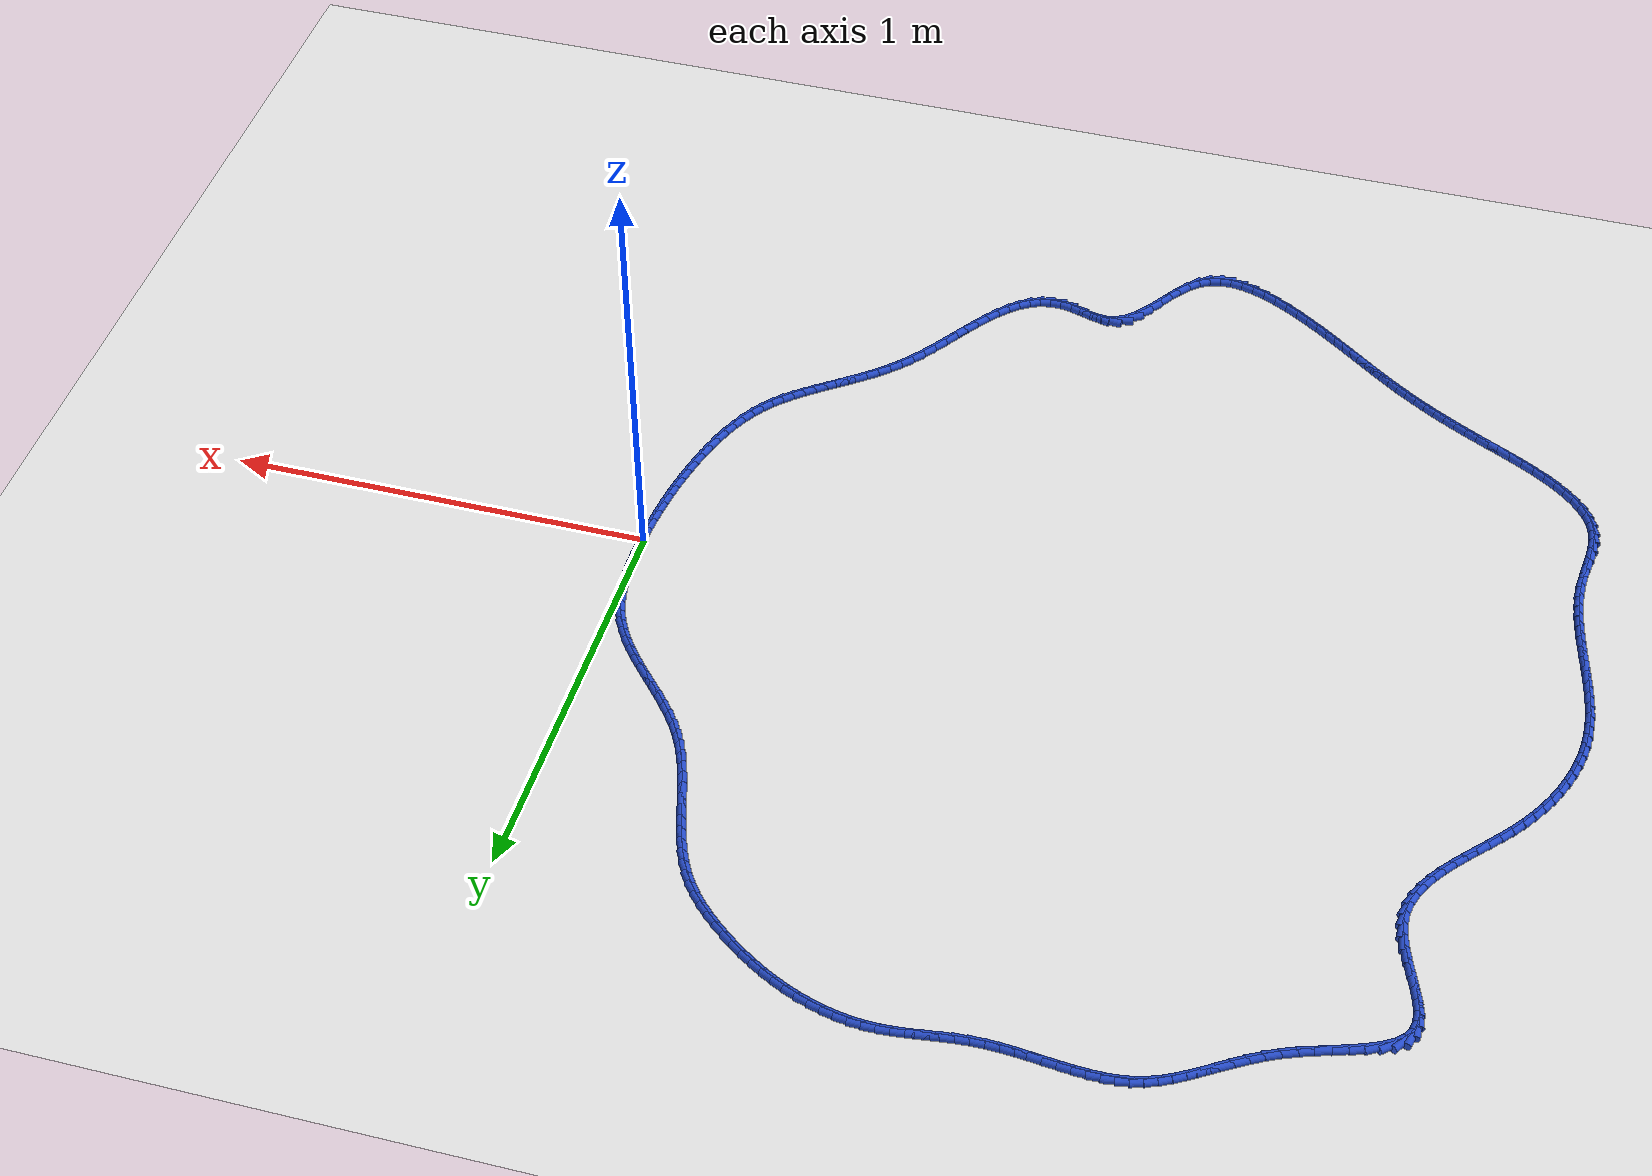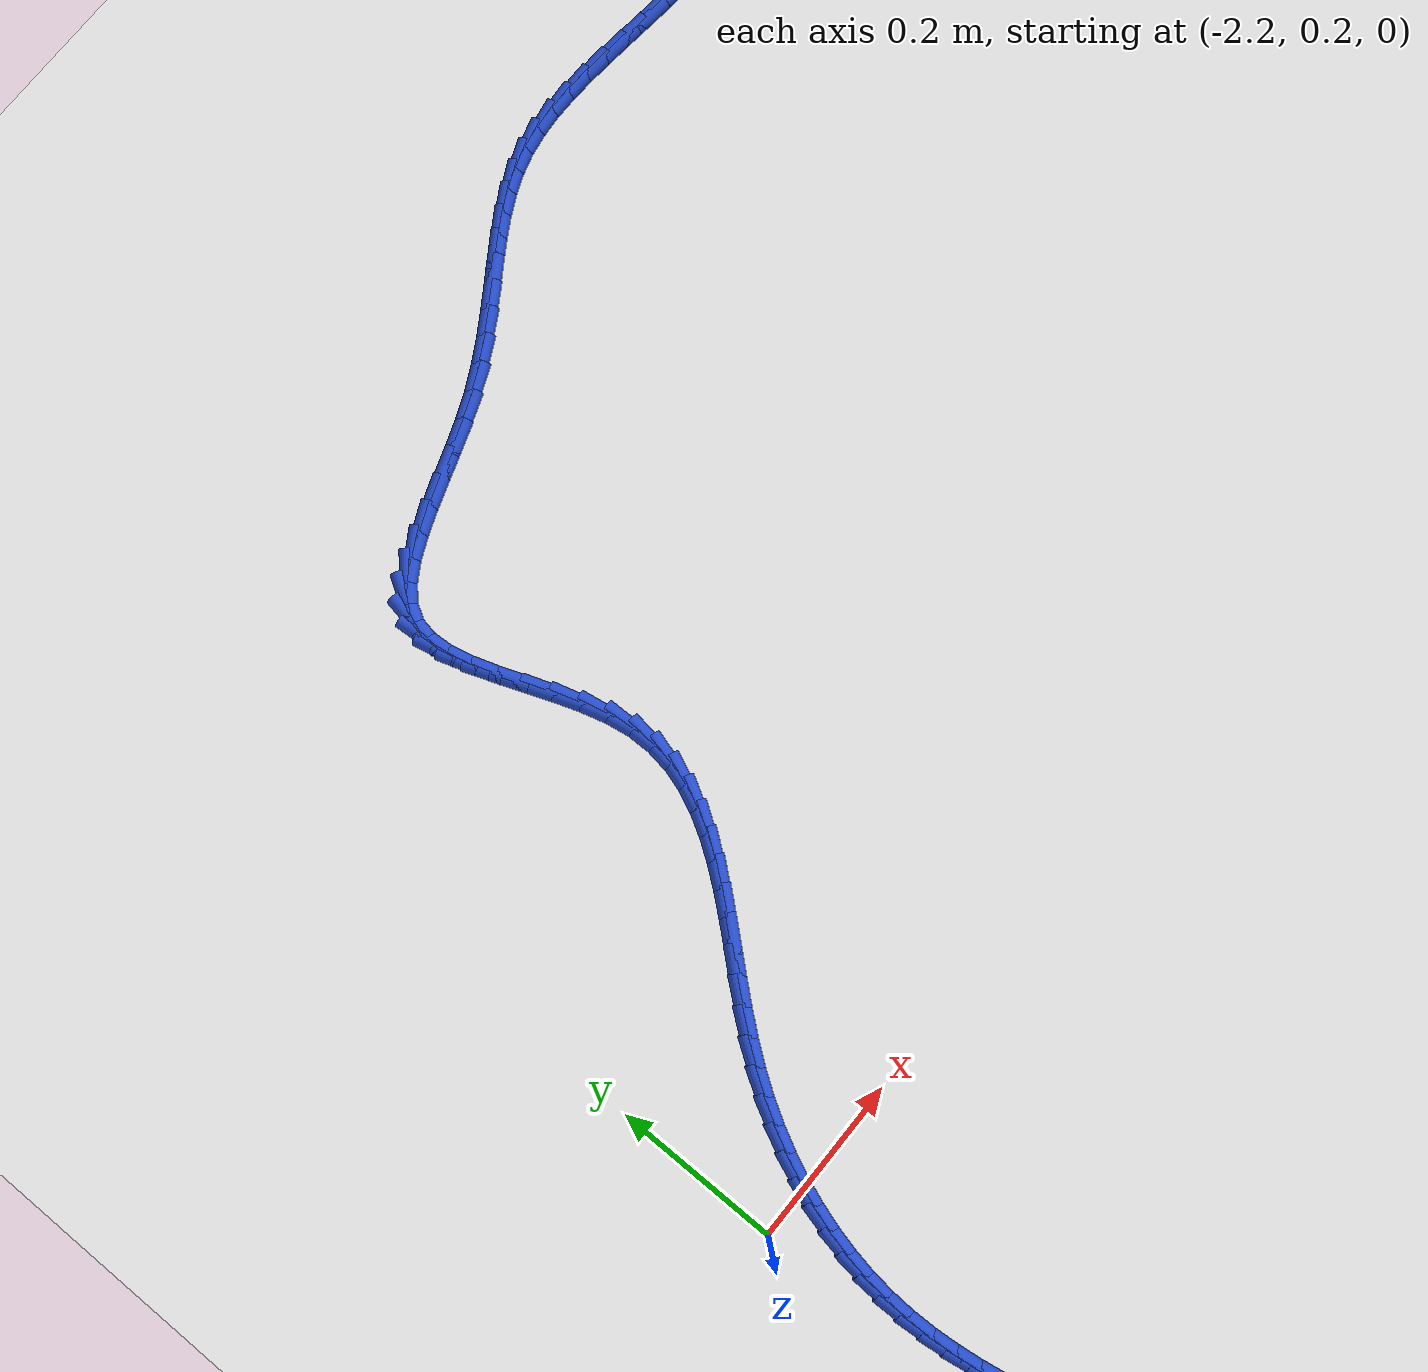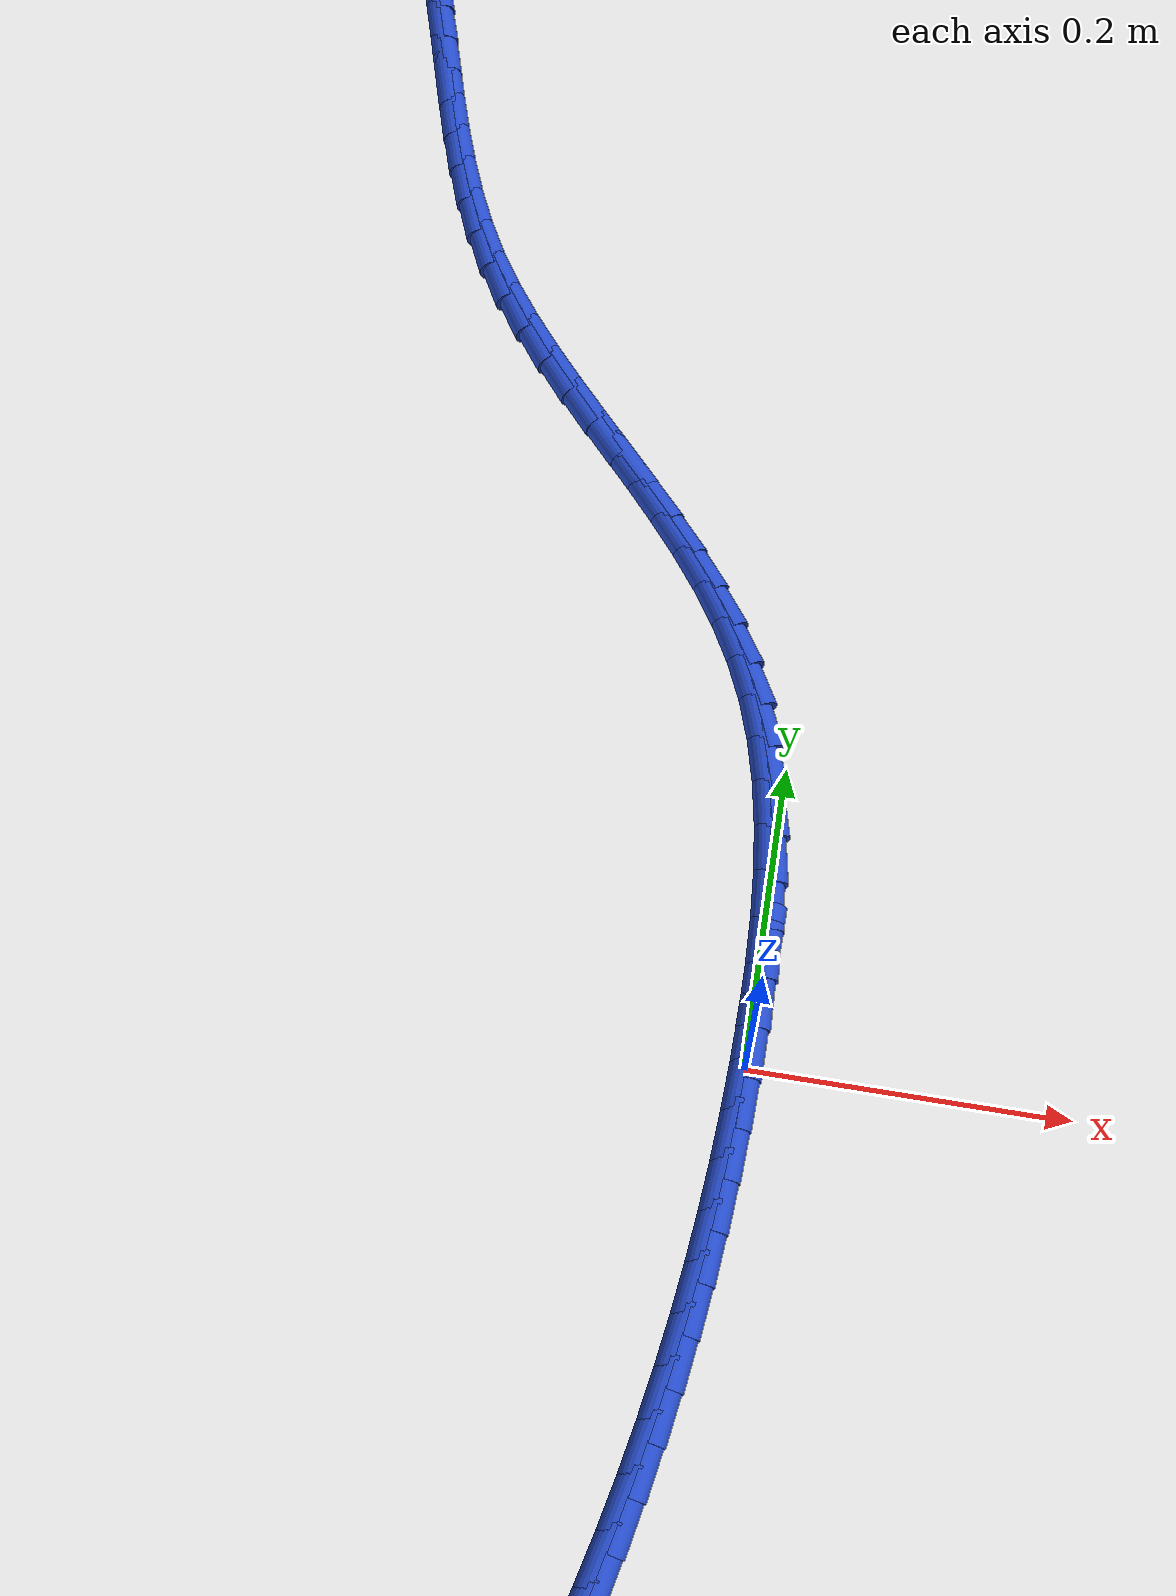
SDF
<sdf version="1.6">
 <world name="default">
  <light name="sun" type="directional">
   <pose>0 0 10 0 -0 0</pose>
   <diffuse>0.8 0.8 0.8 1</diffuse>
   <specular>0.2 0.2 0.2 1</specular>
   <attenuation>
    <range>1000</range>
    <constant>0.9</constant>
    <linear>0.01</linear>
    <quadratic>0.001</quadratic>
   </attenuation>
   <direction>-0.5 0.1 -0.9</direction>
  </light>
  <model name="ground_plane">
   <static>1</static>
   <link name="link">
    <collision name="collision">
     <geometry><plane><normal>0 0 1</normal><size>100 100</size></plane></geometry>
     <surface><friction><ode><mu>100</mu><mu2>50</mu2></ode></friction></surface>
    </collision>
    <visual name="visual">
     <cast_shadows>0</cast_shadows>
     <geometry><plane><normal>0 0 1</normal><size>100 100</size></plane></geometry>
     <material>
      <script><uri>file://media/materials/scripts/gazebo.material</uri><name>Gazebo/WhiteGlow</name></script>
     </material>
    </visual>
   </link>
  </model>
  <gravity>0 0 -9.8</gravity>
  <magnetic_field>6e-06 2.3e-05 -4.2e-05</magnetic_field>
  <atmosphere type="adiabatic"/>
  <physics name="default_physics" default="0" type="ode">
   <max_step_size>0.001</max_step_size>
   <real_time_factor>1</real_time_factor>
   <real_time_update_rate>1000</real_time_update_rate>
  </physics>
  <scene><ambient>0.4 0.4 0.4 1</ambient><background>0.7 0.7 0.7 1</background><shadows>1</shadows></scene>
  <spherical_coordinates>
   <surface_model>EARTH_WGS84</surface_model>
   <latitude_deg>0</latitude_deg>
   <longitude_deg>0</longitude_deg>
   <elevation>0</elevation>
   <heading_deg>0</heading_deg>
  </spherical_coordinates>
  <model name="line">
   <link name="link_0">
    <pose>2.4936649967166602e-17 5.551115123125783e-17 0.01 0 1.57 1.5411175155558543</pose>
    <collision name="collision">
     <geometry><cylinder><radius>0.01</radius><length>0.08</length></cylinder></geometry>
    </collision>
    <visual name="visual">
     <material>
      <script><name>Gazebo/Blue</name><uri>file://media/materials/scripts/gazebo.material</uri></script>
     </material>
     <geometry><cylinder><radius>0.01</radius><length>0.08</length></cylinder></geometry>
    </visual>
   </link>
   <link name="link_1">
    <pose>0.0009247249539259656 0.03114860030866323 0.01 0 1.57 1.566804197083188</pose>
    <collision name="collision">
     <geometry><cylinder><radius>0.01</radius><length>0.08</length></cylinder></geometry>
    </collision>
    <visual name="visual">
     <material>
      <script><name>Gazebo/Blue</name><uri>file://media/materials/scripts/gazebo.material</uri></script>
     </material>
     <geometry><cylinder><radius>0.01</radius><length>0.08</length></cylinder></geometry>
    </visual>
   </link>
   <link name="link_2">
    <pose>0.0010497529973194828 0.062467066447506464 0.01 0 1.57 -1.541951702423499</pose>
    <collision name="collision">
     <geometry><cylinder><radius>0.01</radius><length>0.08</length></cylinder></geometry>
    </collision>
    <visual name="visual">
     <material>
      <script><name>Gazebo/Blue</name><uri>file://media/materials/scripts/gazebo.material</uri></script>
     </material>
     <geometry><cylinder><radius>0.01</radius><length>0.08</length></cylinder></geometry>
    </visual>
   </link>
   <link name="link_3">
    <pose>0.00014661214302193084 0.09376892546965007 0.01 0 1.57 -1.5014585749569875</pose>
    <collision name="collision">
     <geometry><cylinder><radius>0.01</radius><length>0.08</length></cylinder></geometry>
    </collision>
    <visual name="visual">
     <material>
      <script><name>Gazebo/Blue</name><uri>file://media/materials/scripts/gazebo.material</uri></script>
     </material>
     <geometry><cylinder><radius>0.01</radius><length>0.08</length></cylinder></geometry>
    </visual>
   </link>
   <link name="link_4">
    <pose>-0.002013169596125335 0.12486770442821435 0.01 0 1.57 -1.4526584714905681</pose>
    <collision name="collision">
     <geometry><cylinder><radius>0.01</radius><length>0.08</length></cylinder></geometry>
    </collision>
    <visual name="visual">
     <material>
      <script><name>Gazebo/Blue</name><uri>file://media/materials/scripts/gazebo.material</uri></script>
     </material>
     <geometry><cylinder><radius>0.01</radius><length>0.08</length></cylinder></geometry>
    </visual>
   </link>
   <link name="link_5">
    <pose>-0.005658064207280955 0.15557693037631962 0.01 0 1.57 -1.3948095371145166</pose>
    <collision name="collision">
     <geometry><cylinder><radius>0.01</radius><length>0.08</length></cylinder></geometry>
    </collision>
    <visual name="visual">
     <material>
      <script><name>Gazebo/Blue</name><uri>file://media/materials/scripts/gazebo.material</uri></script>
     </material>
     <geometry><cylinder><radius>0.01</radius><length>0.08</length></cylinder></geometry>
    </visual>
   </link>
   <link name="link_6">
    <pose>-0.011016543677603586 0.18571013036708628 0.01 0 1.57 -1.3271684506925083</pose>
    <collision name="collision">
     <geometry><cylinder><radius>0.01</radius><length>0.08</length></cylinder></geometry>
    </collision>
    <visual name="visual">
     <material>
      <script><name>Gazebo/Blue</name><uri>file://media/materials/scripts/gazebo.material</uri></script>
     </material>
     <geometry><cylinder><radius>0.01</radius><length>0.08</length></cylinder></geometry>
    </visual>
   </link>
   <link name="link_7">
    <pose>-0.018317079994251854 0.21508083145363457 0.01 0 1.57 -1.2491358518005122</pose>
    <collision name="collision">
     <geometry><cylinder><radius>0.01</radius><length>0.08</length></cylinder></geometry>
    </collision>
    <visual name="visual">
     <material>
      <script><name>Gazebo/Blue</name><uri>file://media/materials/scripts/gazebo.material</uri></script>
     </material>
     <geometry><cylinder><radius>0.01</radius><length>0.08</length></cylinder></geometry>
    </visual>
   </link>
   <link name="link_8">
    <pose>-0.027788145144384407 0.24350256068908477 0.01 0 1.57 -1.1608087016327475</pose>
    <collision name="collision">
     <geometry><cylinder><radius>0.01</radius><length>0.08</length></cylinder></geometry>
    </collision>
    <visual name="visual">
     <material>
      <script><name>Gazebo/Blue</name><uri>file://media/materials/scripts/gazebo.material</uri></script>
     </material>
     <geometry><cylinder><radius>0.01</radius><length>0.08</length></cylinder></geometry>
    </visual>
   </link>
   <link name="link_9">
    <pose>-0.0396495886026536 0.2707943079459321 0.01 0 1.57 -1.0729803325183473</pose>
    <collision name="collision">
     <geometry><cylinder><radius>0.01</radius><length>0.08</length></cylinder></geometry>
    </collision>
    <visual name="visual">
     <material>
      <script><name>Gazebo/Blue</name><uri>file://media/materials/scripts/gazebo.material</uri></script>
     </material>
     <geometry><cylinder><radius>0.01</radius><length>0.08</length></cylinder></geometry>
    </visual>
   </link>
   <link name="link_10">
    <pose>-0.05385948461010124 0.29694091160277364 0.01 0 1.57 -0.9986812177546561</pose>
    <collision name="collision">
     <geometry><cylinder><radius>0.01</radius><length>0.08</length></cylinder></geometry>
    </collision>
    <visual name="visual">
     <material>
      <script><name>Gazebo/Blue</name><uri>file://media/materials/scripts/gazebo.material</uri></script>
     </material>
     <geometry><cylinder><radius>0.01</radius><length>0.08</length></cylinder></geometry>
    </visual>
   </link>
   <link name="link_11">
    <pose>-0.07007311293765128 0.3221190464080275 0.01 0 1.57 -0.9389917101842004</pose>
    <collision name="collision">
     <geometry><cylinder><radius>0.01</radius><length>0.08</length></cylinder></geometry>
    </collision>
    <visual name="visual">
     <material>
      <script><name>Gazebo/Blue</name><uri>file://media/materials/scripts/gazebo.material</uri></script>
     </material>
     <geometry><cylinder><radius>0.01</radius><length>0.08</length></cylinder></geometry>
    </visual>
   </link>
   <link name="link_12">
    <pose>-0.08792887246290777 0.34651608205210566 0.01 0 1.57 -0.8936611405011107</pose>
    <collision name="collision">
     <geometry><cylinder><radius>0.01</radius><length>0.08</length></cylinder></geometry>
    </collision>
    <visual name="visual">
     <material>
      <script><name>Gazebo/Blue</name><uri>file://media/materials/scripts/gazebo.material</uri></script>
     </material>
     <geometry><cylinder><radius>0.01</radius><length>0.08</length></cylinder></geometry>
    </visual>
   </link>
   <link name="link_13">
    <pose>-0.10706516206347466 0.37031938822541954 0.01 0 1.57 -0.862152978472473</pose>
    <collision name="collision">
     <geometry><cylinder><radius>0.01</radius><length>0.08</length></cylinder></geometry>
    </collision>
    <visual name="visual">
     <material>
      <script><name>Gazebo/Blue</name><uri>file://media/materials/scripts/gazebo.material</uri></script>
     </material>
     <geometry><cylinder><radius>0.01</radius><length>0.08</length></cylinder></geometry>
    </visual>
   </link>
   <link name="link_14">
    <pose>-0.12712038061695605 0.3937163346183811 0.01 0 1.57 -0.8439149859593875</pose>
    <collision name="collision">
     <geometry><cylinder><radius>0.01</radius><length>0.08</length></cylinder></geometry>
    </collision>
    <visual name="visual">
     <material>
      <script><name>Gazebo/Blue</name><uri>file://media/materials/scripts/gazebo.material</uri></script>
     </material>
     <geometry><cylinder><radius>0.01</radius><length>0.08</length></cylinder></geometry>
    </visual>
   </link>
   <link name="link_15">
    <pose>-0.14773292700095586 0.4168942909214019 0.01 0 1.57 -0.8385407450142685</pose>
    <collision name="collision">
     <geometry><cylinder><radius>0.01</radius><length>0.08</length></cylinder></geometry>
    </collision>
    <visual name="visual">
     <material>
      <script><name>Gazebo/Blue</name><uri>file://media/materials/scripts/gazebo.material</uri></script>
     </material>
     <geometry><cylinder><radius>0.01</radius><length>0.08</length></cylinder></geometry>
    </visual>
   </link>
   <link name="link_16">
    <pose>-0.16854120009307821 0.4400406268248937 0.01 0 1.57 -0.8458482087813703</pose>
    <collision name="collision">
     <geometry><cylinder><radius>0.01</radius><length>0.08</length></cylinder></geometry>
    </collision>
    <visual name="visual">
     <material>
      <script><name>Gazebo/Blue</name><uri>file://media/materials/scripts/gazebo.material</uri></script>
     </material>
     <geometry><cylinder><radius>0.01</radius><length>0.08</length></cylinder></geometry>
    </visual>
   </link>
   <link name="link_17">
    <pose>-0.18918359877092705 0.4633427120192683 0.01 0 1.57 -0.8658972939452431</pose>
    <collision name="collision">
     <geometry><cylinder><radius>0.01</radius><length>0.08</length></cylinder></geometry>
    </collision>
    <visual name="visual">
     <material>
      <script><name>Gazebo/Blue</name><uri>file://media/materials/scripts/gazebo.material</uri></script>
     </material>
     <geometry><cylinder><radius>0.01</radius><length>0.08</length></cylinder></geometry>
    </visual>
   </link>
   <link name="link_18">
    <pose>-0.20929852191210643 0.4869879161949373 0.01 0 1.57 -0.8989552329183907</pose>
    <collision name="collision">
     <geometry><cylinder><radius>0.01</radius><length>0.08</length></cylinder></geometry>
    </collision>
    <visual name="visual">
     <material>
      <script><name>Gazebo/Blue</name><uri>file://media/materials/scripts/gazebo.material</uri></script>
     </material>
     <geometry><cylinder><radius>0.01</radius><length>0.08</length></cylinder></geometry>
    </visual>
   </link>
   <link name="link_19">
    <pose>-0.22852436839422038 0.5111636090423126 0.01 0 1.57 -0.9454038836693864</pose>
    <collision name="collision">
     <geometry><cylinder><radius>0.01</radius><length>0.08</length></cylinder></geometry>
    </collision>
    <visual name="visual">
     <material>
      <script><name>Gazebo/Blue</name><uri>file://media/materials/scripts/gazebo.material</uri></script>
     </material>
     <geometry><cylinder><radius>0.01</radius><length>0.08</length></cylinder></geometry>
    </visual>
   </link>
   <link name="link_20">
    <pose>-0.24649953709487288 0.5360571602518056 0.01 0 1.57 -1.005572573166083</pose>
    <collision name="collision">
     <geometry><cylinder><radius>0.01</radius><length>0.08</length></cylinder></geometry>
    </collision>
    <visual name="visual">
     <material>
      <script><name>Gazebo/Blue</name><uri>file://media/materials/scripts/gazebo.material</uri></script>
     </material>
     <geometry><cylinder><radius>0.01</radius><length>0.08</length></cylinder></geometry>
    </visual>
   </link>
   <link name="link_21">
    <pose>-0.2628624268916679 0.5618559395138283 0.01 0 1.57 -1.0756817864464938</pose>
    <collision name="collision">
     <geometry><cylinder><radius>0.01</radius><length>0.08</length></cylinder></geometry>
    </collision>
    <visual name="visual">
     <material>
      <script><name>Gazebo/Blue</name><uri>file://media/materials/scripts/gazebo.material</uri></script>
     </material>
     <geometry><cylinder><radius>0.01</radius><length>0.08</length></cylinder></geometry>
    </visual>
   </link>
   <link name="link_22">
    <pose>-0.2773531183460129 0.5886917550924509 0.01 0 1.57 -1.1386581302464147</pose>
    <collision name="collision">
     <geometry><cylinder><radius>0.01</radius><length>0.08</length></cylinder></geometry>
    </collision>
    <visual name="visual">
     <material>
      <script><name>Gazebo/Blue</name><uri>file://media/materials/scripts/gazebo.material</uri></script>
     </material>
     <geometry><cylinder><radius>0.01</radius><length>0.08</length></cylinder></geometry>
    </visual>
   </link>
   <link name="link_23">
    <pose>-0.29015697139455343 0.6164531034154008 0.01 0 1.57 -1.189663812116927</pose>
    <collision name="collision">
     <geometry><cylinder><radius>0.01</radius><length>0.08</length></cylinder></geometry>
    </collision>
    <visual name="visual">
     <material>
      <script><name>Gazebo/Blue</name><uri>file://media/materials/scripts/gazebo.material</uri></script>
     </material>
     <geometry><cylinder><radius>0.01</radius><length>0.08</length></cylinder></geometry>
    </visual>
   </link>
   <link name="link_24">
    <pose>-0.3015812003584858 0.644961896613624 0.01 0 1.57 -1.2287862854626088</pose>
    <collision name="collision">
     <geometry><cylinder><radius>0.01</radius><length>0.08</length></cylinder></geometry>
    </collision>
    <visual name="visual">
     <material>
      <script><name>Gazebo/Blue</name><uri>file://media/materials/scripts/gazebo.material</uri></script>
     </material>
     <geometry><cylinder><radius>0.01</radius><length>0.08</length></cylinder></geometry>
    </visual>
   </link>
   <link name="link_25">
    <pose>-0.31193302262040384 0.6740400451452422 0.01 0 1.57 -1.256285978493279</pose>
    <collision name="collision">
     <geometry><cylinder><radius>0.01</radius><length>0.08</length></cylinder></geometry>
    </collision>
    <visual name="visual">
     <material>
      <script><name>Gazebo/Blue</name><uri>file://media/materials/scripts/gazebo.material</uri></script>
     </material>
     <geometry><cylinder><radius>0.01</radius><length>0.08</length></cylinder></geometry>
    </visual>
   </link>
   <link name="link_26">
    <pose>-0.3215196555629017 0.7035094594683765 0.01 0 1.57 -1.272434163234875</pose>
    <collision name="collision">
     <geometry><cylinder><radius>0.01</radius><length>0.08</length></cylinder></geometry>
    </collision>
    <visual name="visual">
     <material>
      <script><name>Gazebo/Blue</name><uri>file://media/materials/scripts/gazebo.material</uri></script>
     </material>
     <geometry><cylinder><radius>0.01</radius><length>0.08</length></cylinder></geometry>
    </visual>
   </link>
   <link name="link_27">
    <pose>-0.3306483165685731 0.7331920500411484 0.01 0 1.57 -1.277407993815817</pose>
    <collision name="collision">
     <geometry><cylinder><radius>0.01</radius><length>0.08</length></cylinder></geometry>
    </collision>
    <visual name="visual">
     <material>
      <script><name>Gazebo/Blue</name><uri>file://media/materials/scripts/gazebo.material</uri></script>
     </material>
     <geometry><cylinder><radius>0.01</radius><length>0.08</length></cylinder></geometry>
    </visual>
   </link>
   <link name="link_28">
    <pose>-0.339626223020012 0.7629097273216794 0.01 0 1.57 -1.2712330391350557</pose>
    <collision name="collision">
     <geometry><cylinder><radius>0.01</radius><length>0.08</length></cylinder></geometry>
    </collision>
    <visual name="visual">
     <material>
      <script><name>Gazebo/Blue</name><uri>file://media/materials/scripts/gazebo.material</uri></script>
     </material>
     <geometry><cylinder><radius>0.01</radius><length>0.08</length></cylinder></geometry>
    </visual>
   </link>
   <link name="link_29">
    <pose>-0.34876059229981227 0.7924844017680911 0.01 0 1.57 -1.2537647110883685</pose>
    <collision name="collision">
     <geometry><cylinder><radius>0.01</radius><length>0.08</length></cylinder></geometry>
    </collision>
    <visual name="visual">
     <material>
      <script><name>Gazebo/Blue</name><uri>file://media/materials/scripts/gazebo.material</uri></script>
     </material>
     <geometry><cylinder><radius>0.01</radius><length>0.08</length></cylinder></geometry>
    </visual>
   </link>
   <link name="link_30">
    <pose>-0.35835864179056787 0.821737983838505 0.01 0 1.57 -1.2247062890589913</pose>
    <collision name="collision">
     <geometry><cylinder><radius>0.01</radius><length>0.08</length></cylinder></geometry>
    </collision>
    <visual name="visual">
     <material>
      <script><name>Gazebo/Blue</name><uri>file://media/materials/scripts/gazebo.material</uri></script>
     </material>
     <geometry><cylinder><radius>0.01</radius><length>0.08</length></cylinder></geometry>
    </visual>
   </link>
   <link name="link_31">
    <pose>-0.36872758887487284 0.8504923839910424 0.01 0 1.57 -1.1836691837615632</pose>
    <collision name="collision">
     <geometry><cylinder><radius>0.01</radius><length>0.08</length></cylinder></geometry>
    </collision>
    <visual name="visual">
     <material>
      <script><name>Gazebo/Blue</name><uri>file://media/materials/scripts/gazebo.material</uri></script>
     </material>
     <geometry><cylinder><radius>0.01</radius><length>0.08</length></cylinder></geometry>
    </visual>
   </link>
   <link name="link_32">
    <pose>-0.3801746509353207 0.8785695126838247 0.01 0 1.57 -1.1302877657501977</pose>
    <collision name="collision">
     <geometry><cylinder><radius>0.01</radius><length>0.08</length></cylinder></geometry>
    </collision>
    <visual name="visual">
     <material>
      <script><name>Gazebo/Blue</name><uri>file://media/materials/scripts/gazebo.material</uri></script>
     </material>
     <geometry><cylinder><radius>0.01</radius><length>0.08</length></cylinder></geometry>
    </visual>
   </link>
   <link name="link_33">
    <pose>-0.3930070453545059 0.9057912803749737 0.01 0 1.57 -1.0644019238452715</pose>
    <collision name="collision">
     <geometry><cylinder><radius>0.01</radius><length>0.08</length></cylinder></geometry>
    </collision>
    <visual name="visual">
     <material>
      <script><name>Gazebo/Blue</name><uri>file://media/materials/scripts/gazebo.material</uri></script>
     </material>
     <geometry><cylinder><radius>0.01</radius><length>0.08</length></cylinder></geometry>
    </visual>
   </link>
   <link name="link_34">
    <pose>-0.4075319895150218 0.9319795975226104 0.01 0 1.57 -0.9864521860672946</pose>
    <collision name="collision">
     <geometry><cylinder><radius>0.01</radius><length>0.08</length></cylinder></geometry>
    </collision>
    <visual name="visual">
     <material>
      <script><name>Gazebo/Blue</name><uri>file://media/materials/scripts/gazebo.material</uri></script>
     </material>
     <geometry><cylinder><radius>0.01</radius><length>0.08</length></cylinder></geometry>
    </visual>
   </link>
   <link name="link_35">
    <pose>-0.4240528685556655 0.956958434204447 0.01 0 1.57 -0.9055952675108673</pose>
    <collision name="collision">
     <geometry><cylinder><radius>0.01</radius><length>0.08</length></cylinder></geometry>
    </collision>
    <visual name="visual">
     <material>
      <script><name>Gazebo/Blue</name><uri>file://media/materials/scripts/gazebo.material</uri></script>
     </material>
     <geometry><cylinder><radius>0.01</radius><length>0.08</length></cylinder></geometry>
    </visual>
   </link>
   <link name="link_36">
    <pose>-0.4426536823417337 0.9806696679777407 0.01 0 1.57 -0.835000655140958</pose>
    <collision name="collision">
     <geometry><cylinder><radius>0.01</radius><length>0.08</length></cylinder></geometry>
    </collision>
    <visual name="visual">
     <material>
      <script><name>Gazebo/Blue</name><uri>file://media/materials/scripts/gazebo.material</uri></script>
     </material>
     <geometry><cylinder><radius>0.01</radius><length>0.08</length></cylinder></geometry>
    </visual>
   </link>
   <link name="link_37">
    <pose>-0.46308431459804655 1.003234745389823 0.01 0 1.57 -0.7755948475873455</pose>
    <collision name="collision">
     <geometry><cylinder><radius>0.01</radius><length>0.08</length></cylinder></geometry>
    </collision>
    <visual name="visual">
     <material>
      <script><name>Gazebo/Blue</name><uri>file://media/materials/scripts/gazebo.material</uri></script>
     </material>
     <geometry><cylinder><radius>0.01</radius><length>0.08</length></cylinder></geometry>
    </visual>
   </link>
   <link name="link_38">
    <pose>-0.4850665900722247 1.0247901931400654 0.01 0 1.57 -0.7268962510684988</pose>
    <collision name="collision">
     <geometry><cylinder><radius>0.01</radius><length>0.08</length></cylinder></geometry>
    </collision>
    <visual name="visual">
     <material>
      <script><name>Gazebo/Blue</name><uri>file://media/materials/scripts/gazebo.material</uri></script>
     </material>
     <geometry><cylinder><radius>0.01</radius><length>0.08</length></cylinder></geometry>
    </visual>
   </link>
   <link name="link_39">
    <pose>-0.5083223335118897 1.0454725379278413 0.01 0 1.57 -0.6874005775575889</pose>
    <collision name="collision">
     <geometry><cylinder><radius>0.01</radius><length>0.08</length></cylinder></geometry>
    </collision>
    <visual name="visual">
     <material>
      <script><name>Gazebo/Blue</name><uri>file://media/materials/scripts/gazebo.material</uri></script>
     </material>
     <geometry><cylinder><radius>0.01</radius><length>0.08</length></cylinder></geometry>
    </visual>
   </link>
   <link name="link_40">
    <pose>-0.5325909647073878 1.0653964860336338 0.01 0 1.57 -0.6500074067774555</pose>
    <collision name="collision">
     <geometry><cylinder><radius>0.01</radius><length>0.08</length></cylinder></geometry>
    </collision>
    <visual name="visual">
     <material>
      <script><name>Gazebo/Blue</name><uri>file://media/materials/scripts/gazebo.material</uri></script>
     </material>
     <geometry><cylinder><radius>0.01</radius><length>0.08</length></cylinder></geometry>
    </visual>
   </link>
   <link name="link_41">
    <pose>-0.5577413488123795 1.0845162126102197 0.01 0 1.57 -0.6114201795143959</pose>
    <collision name="collision">
     <geometry><cylinder><radius>0.01</radius><length>0.08</length></cylinder></geometry>
    </collision>
    <visual name="visual">
     <material>
      <script><name>Gazebo/Blue</name><uri>file://media/materials/scripts/gazebo.material</uri></script>
     </material>
     <geometry><cylinder><radius>0.01</radius><length>0.08</length></cylinder></geometry>
    </visual>
   </link>
   <link name="link_42">
    <pose>-0.583700137542635 1.102714229046263 0.01 0 1.57 -0.5712840585881714</pose>
    <collision name="collision">
     <geometry><cylinder><radius>0.01</radius><length>0.08</length></cylinder></geometry>
    </collision>
    <visual name="visual">
     <material>
      <script><name>Gazebo/Blue</name><uri>file://media/materials/scripts/gazebo.material</uri></script>
     </material>
     <geometry><cylinder><radius>0.01</radius><length>0.08</length></cylinder></geometry>
    </visual>
   </link>
   <link name="link_43">
    <pose>-0.6103942502731757 1.119872714793924 0.01 0 1.57 -0.5292535076300824</pose>
    <collision name="collision">
     <geometry><cylinder><radius>0.01</radius><length>0.08</length></cylinder></geometry>
    </collision>
    <visual name="visual">
     <material>
      <script><name>Gazebo/Blue</name><uri>file://media/materials/scripts/gazebo.material</uri></script>
     </material>
     <geometry><cylinder><radius>0.01</radius><length>0.08</length></cylinder></geometry>
    </visual>
   </link>
   <link name="link_44">
    <pose>-0.6377506063790225 1.1358738493053622 0.01 0 1.57 -0.48497644131076717</pose>
    <collision name="collision">
     <geometry><cylinder><radius>0.01</radius><length>0.08</length></cylinder></geometry>
    </collision>
    <visual name="visual">
     <material>
      <script><name>Gazebo/Blue</name><uri>file://media/materials/scripts/gazebo.material</uri></script>
     </material>
     <geometry><cylinder><radius>0.01</radius><length>0.08</length></cylinder></geometry>
    </visual>
   </link>
   <link name="link_45">
    <pose>-0.6656961252351976 1.1505998120327388 0.01 0 1.57 -0.4380944187464054</pose>
    <collision name="collision">
     <geometry><cylinder><radius>0.01</radius><length>0.08</length></cylinder></geometry>
    </collision>
    <visual name="visual">
     <material>
      <script><name>Gazebo/Blue</name><uri>file://media/materials/scripts/gazebo.material</uri></script>
     </material>
     <geometry><cylinder><radius>0.01</radius><length>0.08</length></cylinder></geometry>
    </visual>
   </link>
   <link name="link_46">
    <pose>-0.6941577262167213 1.163932782428213 0.01 0 1.57 -0.38824602931086394</pose>
    <collision name="collision">
     <geometry><cylinder><radius>0.01</radius><length>0.08</length></cylinder></geometry>
    </collision>
    <visual name="visual">
     <material>
      <script><name>Gazebo/Blue</name><uri>file://media/materials/scripts/gazebo.material</uri></script>
     </material>
     <geometry><cylinder><radius>0.01</radius><length>0.08</length></cylinder></geometry>
    </visual>
   </link>
   <link name="link_47">
    <pose>-0.7230623286986153 1.1757549399439458 0.01 0 1.57 -0.3350744713239371</pose>
    <collision name="collision">
     <geometry><cylinder><radius>0.01</radius><length>0.08</length></cylinder></geometry>
    </collision>
    <visual name="visual">
     <material>
      <script><name>Gazebo/Blue</name><uri>file://media/materials/scripts/gazebo.material</uri></script>
     </material>
     <geometry><cylinder><radius>0.01</radius><length>0.08</length></cylinder></geometry>
    </visual>
   </link>
   <link name="link_48">
    <pose>-0.7523368520559008 1.1859484640320972 0.01 0 1.57 -0.2782405397573371</pose>
    <collision name="collision">
     <geometry><cylinder><radius>0.01</radius><length>0.08</length></cylinder></geometry>
    </collision>
    <visual name="visual">
     <material>
      <script><name>Gazebo/Blue</name><uri>file://media/materials/scripts/gazebo.material</uri></script>
     </material>
     <geometry><cylinder><radius>0.01</radius><length>0.08</length></cylinder></geometry>
    </visual>
   </link>
   <link name="link_49">
    <pose>-0.7819082156635991 1.1943955341448278 0.01 0 1.57 -0.21744228618995098</pose>
    <collision name="collision">
     <geometry><cylinder><radius>0.01</radius><length>0.08</length></cylinder></geometry>
    </collision>
    <visual name="visual">
     <material>
      <script><name>Gazebo/Blue</name><uri>file://media/materials/scripts/gazebo.material</uri></script>
     </material>
     <geometry><cylinder><radius>0.01</radius><length>0.08</length></cylinder></geometry>
    </visual>
   </link>
   <link name="link_50">
    <pose>-0.8117033388967313 1.2009783297342966 0.01 0 1.57 -0.15244230610303708</pose>
    <collision name="collision">
     <geometry><cylinder><radius>0.01</radius><length>0.08</length></cylinder></geometry>
    </collision>
    <visual name="visual">
     <material>
      <script><name>Gazebo/Blue</name><uri>file://media/materials/scripts/gazebo.material</uri></script>
     </material>
     <geometry><cylinder><radius>0.01</radius><length>0.08</length></cylinder></geometry>
    </visual>
   </link>
   <link name="link_51">
    <pose>-0.8416491411303186 1.205579030252665 0.01 0 1.57 -0.08310269130032742</pose>
    <collision name="collision">
     <geometry><cylinder><radius>0.01</radius><length>0.08</length></cylinder></geometry>
    </collision>
    <visual name="visual">
     <material>
      <script><name>Gazebo/Blue</name><uri>file://media/materials/scripts/gazebo.material</uri></script>
     </material>
     <geometry><cylinder><radius>0.01</radius><length>0.08</length></cylinder></geometry>
    </visual>
   </link>
   <link name="link_52">
    <pose>-0.8716725417393829 1.208079815152093 0.01 0 1.57 -0.009743853470388659</pose>
    <collision name="collision">
     <geometry><cylinder><radius>0.01</radius><length>0.08</length></cylinder></geometry>
    </collision>
    <visual name="visual">
     <material>
      <script><name>Gazebo/Blue</name><uri>file://media/materials/scripts/gazebo.material</uri></script>
     </material>
     <geometry><cylinder><radius>0.01</radius><length>0.08</length></cylinder></geometry>
    </visual>
   </link>
   <link name="link_53">
    <pose>-0.9017021887058433 1.2083724288924713 0.01 0 1.57 0.056738624834997475</pose>
    <collision name="collision">
     <geometry><cylinder><radius>0.01</radius><length>0.08</length></cylinder></geometry>
    </collision>
    <visual name="visual">
     <material>
      <script><name>Gazebo/Blue</name><uri>file://media/materials/scripts/gazebo.material</uri></script>
     </material>
     <geometry><cylinder><radius>0.01</radius><length>0.08</length></cylinder></geometry>
    </visual>
   </link>
   <link name="link_54">
    <pose>-0.9317243024667585 1.2066671851693243 0.01 0 1.57 0.10297110367970945</pose>
    <collision name="collision">
     <geometry><cylinder><radius>0.01</radius><length>0.08</length></cylinder></geometry>
    </collision>
    <visual name="visual">
     <material>
      <script><name>Gazebo/Blue</name><uri>file://media/materials/scripts/gazebo.material</uri></script>
     </material>
     <geometry><cylinder><radius>0.01</radius><length>0.08</length></cylinder></geometry>
    </visual>
   </link>
   <link name="link_55">
    <pose>-0.9617947554054873 1.2035598071112181 0.01 0 1.57 0.12821438423738282</pose>
    <collision name="collision">
     <geometry><cylinder><radius>0.01</radius><length>0.08</length></cylinder></geometry>
    </collision>
    <visual name="visual">
     <material>
      <script><name>Gazebo/Blue</name><uri>file://media/materials/scripts/gazebo.material</uri></script>
     </material>
     <geometry><cylinder><radius>0.01</radius><length>0.08</length></cylinder></geometry>
    </visual>
   </link>
   <link name="link_56">
    <pose>-0.991973591917718 1.1996691031012097 0.01 0 1.57 0.13284030654886989</pose>
    <collision name="collision">
     <geometry><cylinder><radius>0.01</radius><length>0.08</length></cylinder></geometry>
    </collision>
    <visual name="visual">
     <material>
      <script><name>Gazebo/Blue</name><uri>file://media/materials/scripts/gazebo.material</uri></script>
     </material>
     <geometry><cylinder><radius>0.01</radius><length>0.08</length></cylinder></geometry>
    </visual>
   </link>
   <link name="link_57">
    <pose>-1.0223208563991373 1.1956138815223551 0.01 0 1.57 0.11723085197073539</pose>
    <collision name="collision">
     <geometry><cylinder><radius>0.01</radius><length>0.08</length></cylinder></geometry>
    </collision>
    <visual name="visual">
     <material>
      <script><name>Gazebo/Blue</name><uri>file://media/materials/scripts/gazebo.material</uri></script>
     </material>
     <geometry><cylinder><radius>0.01</radius><length>0.08</length></cylinder></geometry>
    </visual>
   </link>
   <link name="link_58">
    <pose>-1.0528965932454333 1.1920129507577117 0.01 0 1.57 0.08171919906218206</pose>
    <collision name="collision">
     <geometry><cylinder><radius>0.01</radius><length>0.08</length></cylinder></geometry>
    </collision>
    <visual name="visual">
     <material>
      <script><name>Gazebo/Blue</name><uri>file://media/materials/scripts/gazebo.material</uri></script>
     </material>
     <geometry><cylinder><radius>0.01</radius><length>0.08</length></cylinder></geometry>
    </visual>
   </link>
   <link name="link_59">
    <pose>-1.0837608468522935 1.1894851191903357 0.01 0 1.57 0.027521034413831965</pose>
    <collision name="collision">
     <geometry><cylinder><radius>0.01</radius><length>0.08</length></cylinder></geometry>
    </collision>
    <visual name="visual">
     <material>
      <script><name>Gazebo/Blue</name><uri>file://media/materials/scripts/gazebo.material</uri></script>
     </material>
     <geometry><cylinder><radius>0.01</radius><length>0.08</length></cylinder></geometry>
    </visual>
   </link>
   <link name="link_60">
    <pose>-1.1149693905140685 1.1886260108769489 0.01 0 1.57 -0.02785951372487294</pose>
    <collision name="collision">
     <geometry><cylinder><radius>0.01</radius><length>0.08</length></cylinder></geometry>
    </collision>
    <visual name="visual">
     <material>
      <script><name>Gazebo/Blue</name><uri>file://media/materials/scripts/gazebo.material</uri></script>
     </material>
     <geometry><cylinder><radius>0.01</radius><length>0.08</length></cylinder></geometry>
    </visual>
   </link>
   <link name="link_61">
    <pose>-1.146480890152022 1.1895041331309557 0.01 0 1.57 -0.06808751815411529</pose>
    <collision name="collision">
     <geometry><cylinder><radius>0.01</radius><length>0.08</length></cylinder></geometry>
    </collision>
    <visual name="visual">
     <material>
      <script><name>Gazebo/Blue</name><uri>file://media/materials/scripts/gazebo.material</uri></script>
     </material>
     <geometry><cylinder><radius>0.01</radius><length>0.08</length></cylinder></geometry>
    </visual>
   </link>
   <link name="link_62">
    <pose>-1.1781575268543272 1.1916642557844286 0.01 0 1.57 -0.09324309955599905</pose>
    <collision name="collision">
     <geometry><cylinder><radius>0.01</radius><length>0.08</length></cylinder></geometry>
    </collision>
    <visual name="visual">
     <material>
      <script><name>Gazebo/Blue</name><uri>file://media/materials/scripts/gazebo.material</uri></script>
     </material>
     <geometry><cylinder><radius>0.01</radius><length>0.08</length></cylinder></geometry>
    </visual>
   </link>
   <link name="link_63">
    <pose>-1.209857335117433 1.194628640204265 0.01 0 1.57 -0.10383051137457185</pose>
    <collision name="collision">
     <geometry><cylinder><radius>0.01</radius><length>0.08</length></cylinder></geometry>
    </collision>
    <visual name="visual">
     <material>
      <script><name>Gazebo/Blue</name><uri>file://media/materials/scripts/gazebo.material</uri></script>
     </material>
     <geometry><cylinder><radius>0.01</radius><length>0.08</length></cylinder></geometry>
    </visual>
   </link>
   <link name="link_64">
    <pose>-1.2414383494377874 1.1979195477573623 0.01 0 1.57 -0.09991100285449732</pose>
    <collision name="collision">
     <geometry><cylinder><radius>0.01</radius><length>0.08</length></cylinder></geometry>
    </collision>
    <visual name="visual">
     <material>
      <script><name>Gazebo/Blue</name><uri>file://media/materials/scripts/gazebo.material</uri></script>
     </material>
     <geometry><cylinder><radius>0.01</radius><length>0.08</length></cylinder></geometry>
    </visual>
   </link>
   <link name="link_65">
    <pose>-1.2727586043118388 1.201059239810617 0.01 0 1.57 -0.0810297749593936</pose>
    <collision name="collision">
     <geometry><cylinder><radius>0.01</radius><length>0.08</length></cylinder></geometry>
    </collision>
    <visual name="visual">
     <material>
      <script><name>Gazebo/Blue</name><uri>file://media/materials/scripts/gazebo.material</uri></script>
     </material>
     <geometry><cylinder><radius>0.01</radius><length>0.08</length></cylinder></geometry>
    </visual>
   </link>
   <link name="link_66">
    <pose>-1.3036761342360377 1.203569977730928 0.01 0 1.57 -0.04619411096270264</pose>
    <collision name="collision">
     <geometry><cylinder><radius>0.01</radius><length>0.08</length></cylinder></geometry>
    </collision>
    <visual name="visual">
     <material>
      <script><name>Gazebo/Blue</name><uri>file://media/materials/scripts/gazebo.material</uri></script>
     </material>
     <geometry><cylinder><radius>0.01</radius><length>0.08</length></cylinder></geometry>
    </visual>
   </link>
   <link name="link_67">
    <pose>-1.3340489737068302 1.2049740228851908 0.01 0 1.57 0.006076362921910204</pose>
    <collision name="collision">
     <geometry><cylinder><radius>0.01</radius><length>0.08</length></cylinder></geometry>
    </collision>
    <visual name="visual">
     <material>
      <script><name>Gazebo/Blue</name><uri>file://media/materials/scripts/gazebo.material</uri></script>
     </material>
     <geometry><cylinder><radius>0.01</radius><length>0.08</length></cylinder></geometry>
    </visual>
   </link>
   <link name="link_68">
    <pose>-1.3637351572206662 1.204793636640304 0.01 0 1.57 0.07755534820530084</pose>
    <collision name="collision">
     <geometry><cylinder><radius>0.01</radius><length>0.08</length></cylinder></geometry>
    </collision>
    <visual name="visual">
     <material>
      <script><name>Gazebo/Blue</name><uri>file://media/materials/scripts/gazebo.material</uri></script>
     </material>
     <geometry><cylinder><radius>0.01</radius><length>0.08</length></cylinder></geometry>
    </visual>
   </link>
   <link name="link_69">
    <pose>-1.3925927192739944 1.202551080363164 0.01 0 1.57 0.1698423925672079</pose>
    <collision name="collision">
     <geometry><cylinder><radius>0.01</radius><length>0.08</length></cylinder></geometry>
    </collision>
    <visual name="visual">
     <material>
      <script><name>Gazebo/Blue</name><uri>file://media/materials/scripts/gazebo.material</uri></script>
     </material>
     <geometry><cylinder><radius>0.01</radius><length>0.08</length></cylinder></geometry>
    </visual>
   </link>
   <link name="link_70">
    <pose>-1.4204796943632636 1.1977686154206686 0.01 0 1.57 0.280938828629561</pose>
    <collision name="collision">
     <geometry><cylinder><radius>0.01</radius><length>0.08</length></cylinder></geometry>
    </collision>
    <visual name="visual">
     <material>
      <script><name>Gazebo/Blue</name><uri>file://media/materials/scripts/gazebo.material</uri></script>
     </material>
     <geometry><cylinder><radius>0.01</radius><length>0.08</length></cylinder></geometry>
    </visual>
   </link>
   <link name="link_71">
    <pose>-1.4472855113593137 1.1900332324352256 0.01 0 1.57 0.3856729244805571</pose>
    <collision name="collision">
     <geometry><cylinder><radius>0.01</radius><length>0.08</length></cylinder></geometry>
    </collision>
    <visual name="visual">
     <material>
      <script><name>Gazebo/Blue</name><uri>file://media/materials/scripts/gazebo.material</uri></script>
     </material>
     <geometry><cylinder><radius>0.01</radius><length>0.08</length></cylinder></geometry>
    </visual>
   </link>
   <link name="link_72">
    <pose>-1.473183998663154 1.1795183000097555 0.01 0 1.57 0.4684083320945837</pose>
    <collision name="collision">
     <geometry><cylinder><radius>0.01</radius><length>0.08</length></cylinder></geometry>
    </collision>
    <visual name="visual">
     <material>
      <script><name>Gazebo/Blue</name><uri>file://media/materials/scripts/gazebo.material</uri></script>
     </material>
     <geometry><cylinder><radius>0.01</radius><length>0.08</length></cylinder></geometry>
    </visual>
   </link>
   <link name="link_73">
    <pose>-1.498500285808388 1.1667091410339063 0.01 0 1.57 0.5279694881150337</pose>
    <collision name="collision">
     <geometry><cylinder><radius>0.01</radius><length>0.08</length></cylinder></geometry>
    </collision>
    <visual name="visual">
     <material>
      <script><name>Gazebo/Blue</name><uri>file://media/materials/scripts/gazebo.material</uri></script>
     </material>
     <geometry><cylinder><radius>0.01</radius><length>0.08</length></cylinder></geometry>
    </visual>
   </link>
   <link name="link_74">
    <pose>-1.5235609054826096 1.1520939714351712 0.01 0 1.57 0.5650337916920652</pose>
    <collision name="collision">
     <geometry><cylinder><radius>0.01</radius><length>0.08</length></cylinder></geometry>
    </collision>
    <visual name="visual">
     <material>
      <script><name>Gazebo/Blue</name><uri>file://media/materials/scripts/gazebo.material</uri></script>
     </material>
     <geometry><cylinder><radius>0.01</radius><length>0.08</length></cylinder></geometry>
    </visual>
   </link>
   <link name="link_75">
    <pose>-1.5486923903734136 1.1361610071410453 0.01 0 1.57 0.5810085819760527</pose>
    <collision name="collision">
     <geometry><cylinder><radius>0.01</radius><length>0.08</length></cylinder></geometry>
    </collision>
    <visual name="visual">
     <material>
      <script><name>Gazebo/Blue</name><uri>file://media/materials/scripts/gazebo.material</uri></script>
     </material>
     <geometry><cylinder><radius>0.01</radius><length>0.08</length></cylinder></geometry>
    </visual>
   </link>
   <link name="link_76">
    <pose>-1.5742212731683944 1.1193984640790218 0.01 0 1.57 0.5774342736609605</pose>
    <collision name="collision">
     <geometry><cylinder><radius>0.01</radius><length>0.08</length></cylinder></geometry>
    </collision>
    <visual name="visual">
     <material>
      <script><name>Gazebo/Blue</name><uri>file://media/materials/scripts/gazebo.material</uri></script>
     </material>
     <geometry><cylinder><radius>0.01</radius><length>0.08</length></cylinder></geometry>
    </visual>
   </link>
   <link name="link_77">
    <pose>-1.6004740865551474 1.102294558176595 0.01 0 1.57 0.5557631479614478</pose>
    <collision name="collision">
     <geometry><cylinder><radius>0.01</radius><length>0.08</length></cylinder></geometry>
    </collision>
    <visual name="visual">
     <material>
      <script><name>Gazebo/Blue</name><uri>file://media/materials/scripts/gazebo.material</uri></script>
     </material>
     <geometry><cylinder><radius>0.01</radius><length>0.08</length></cylinder></geometry>
    </visual>
   </link>
   <link name="link_78">
    <pose>-1.6277773632212666 1.085337505361258 0.01 0 1.57 0.5173900393681569</pose>
    <collision name="collision">
     <geometry><cylinder><radius>0.01</radius><length>0.08</length></cylinder></geometry>
    </collision>
    <visual name="visual">
     <material>
      <script><name>Gazebo/Blue</name><uri>file://media/materials/scripts/gazebo.material</uri></script>
     </material>
     <geometry><cylinder><radius>0.01</radius><length>0.08</length></cylinder></geometry>
    </visual>
   </link>
   <link name="link_79">
    <pose>-1.656457635854347 1.0690155215605055 0.01 0 1.57 0.4638265887498768</pose>
    <collision name="collision">
     <geometry><cylinder><radius>0.01</radius><length>0.08</length></cylinder></geometry>
    </collision>
    <visual name="visual">
     <material>
      <script><name>Gazebo/Blue</name><uri>file://media/materials/scripts/gazebo.material</uri></script>
     </material>
     <geometry><cylinder><radius>0.01</radius><length>0.08</length></cylinder></geometry>
    </visual>
   </link>
   <link name="link_80">
    <pose>-1.6868414371419824 1.053816822701831 0.01 0 1.57 0.39898774823349337</pose>
    <collision name="collision">
     <geometry><cylinder><radius>0.01</radius><length>0.08</length></cylinder></geometry>
    </collision>
    <visual name="visual">
     <material>
      <script><name>Gazebo/Blue</name><uri>file://media/materials/scripts/gazebo.material</uri></script>
     </material>
     <geometry><cylinder><radius>0.01</radius><length>0.08</length></cylinder></geometry>
    </visual>
   </link>
   <link name="link_81">
    <pose>-1.719188342139878 1.0401793503189127 0.01 0 1.57 0.34856916180092057</pose>
    <collision name="collision">
     <geometry><cylinder><radius>0.01</radius><length>0.08</length></cylinder></geometry>
    </collision>
    <visual name="visual">
     <material>
      <script><name>Gazebo/Blue</name><uri>file://media/materials/scripts/gazebo.material</uri></script>
     </material>
     <geometry><cylinder><radius>0.01</radius><length>0.08</length></cylinder></geometry>
    </visual>
   </link>
   <link name="link_82">
    <pose>-1.75292816920245 1.0279180323472181 0.01 0 1.57 0.32590989201044224</pose>
    <collision name="collision">
     <geometry><cylinder><radius>0.01</radius><length>0.08</length></cylinder></geometry>
    </collision>
    <visual name="visual">
     <material>
      <script><name>Gazebo/Blue</name><uri>file://media/materials/scripts/gazebo.material</uri></script>
     </material>
     <geometry><cylinder><radius>0.01</radius><length>0.08</length></cylinder></geometry>
    </visual>
   </link>
   <link name="link_83">
    <pose>-1.786929960382765 1.0164267440681607 0.01 0 1.57 0.32973304284462196</pose>
    <collision name="collision">
     <geometry><cylinder><radius>0.01</radius><length>0.08</length></cylinder></geometry>
    </collision>
    <visual name="visual">
     <material>
      <script><name>Gazebo/Blue</name><uri>file://media/materials/scripts/gazebo.material</uri></script>
     </material>
     <geometry><cylinder><radius>0.01</radius><length>0.08</length></cylinder></geometry>
    </visual>
   </link>
   <link name="link_84">
    <pose>-1.8200521985718534 1.0050914325336804 0.01 0 1.57 0.36244284294760415</pose>
    <collision name="collision">
     <geometry><cylinder><radius>0.01</radius><length>0.08</length></cylinder></geometry>
    </collision>
    <visual name="visual">
     <material>
      <script><name>Gazebo/Blue</name><uri>file://media/materials/scripts/gazebo.material</uri></script>
     </material>
     <geometry><cylinder><radius>0.01</radius><length>0.08</length></cylinder></geometry>
    </visual>
   </link>
   <link name="link_85">
    <pose>-1.8511533666607445 0.993298044795718 0.01 0 1.57 0.4315454453440406</pose>
    <collision name="collision">
     <geometry><cylinder><radius>0.01</radius><length>0.08</length></cylinder></geometry>
    </collision>
    <visual name="visual">
     <material>
      <script><name>Gazebo/Blue</name><uri>file://media/materials/scripts/gazebo.material</uri></script>
     </material>
     <geometry><cylinder><radius>0.01</radius><length>0.08</length></cylinder></geometry>
    </visual>
   </link>
   <link name="link_86">
    <pose>-1.8790919475404686 0.9804325279062152 0.01 0 1.57 0.5518822259734445</pose>
    <collision name="collision">
     <geometry><cylinder><radius>0.01</radius><length>0.08</length></cylinder></geometry>
    </collision>
    <visual name="visual">
     <material>
      <script><name>Gazebo/Blue</name><uri>file://media/materials/scripts/gazebo.material</uri></script>
     </material>
     <geometry><cylinder><radius>0.01</radius><length>0.08</length></cylinder></geometry>
    </visual>
   </link>
   <link name="link_87">
    <pose>-1.9027264241020554 0.9658808289171114 0.01 0 1.57 0.7472633785163912</pose>
    <collision name="collision">
     <geometry><cylinder><radius>0.01</radius><length>0.08</length></cylinder></geometry>
    </collision>
    <visual name="visual">
     <material>
      <script><name>Gazebo/Blue</name><uri>file://media/materials/scripts/gazebo.material</uri></script>
     </material>
     <geometry><cylinder><radius>0.01</radius><length>0.08</length></cylinder></geometry>
    </visual>
   </link>
   <link name="link_88">
    <pose>-1.9209152792365358 0.9490288948803478 0.01 0 1.57 1.0400282239132286</pose>
    <collision name="collision">
     <geometry><cylinder><radius>0.01</radius><length>0.08</length></cylinder></geometry>
    </collision>
    <visual name="visual">
     <material>
      <script><name>Gazebo/Blue</name><uri>file://media/materials/scripts/gazebo.material</uri></script>
     </material>
     <geometry><cylinder><radius>0.01</radius><length>0.08</length></cylinder></geometry>
    </visual>
   </link>
   <link name="link_89">
    <pose>-1.9325170377188372 0.9292626917431306 0.01 0 1.57 1.3839415310409848</pose>
    <collision name="collision">
     <geometry><cylinder><radius>0.01</radius><length>0.08</length></cylinder></geometry>
    </collision>
    <visual name="visual">
     <material>
      <script><name>Gazebo/Blue</name><uri>file://media/materials/scripts/gazebo.material</uri></script>
     </material>
     <geometry><cylinder><radius>0.01</radius><length>0.08</length></cylinder></geometry>
    </visual>
   </link>
   <link name="link_90">
    <pose>-1.9368793821560053 0.9061888613554766 0.01 0 1.57 -1.5007365801726607</pose>
    <collision name="collision">
     <geometry><cylinder><radius>0.01</radius><length>0.08</length></cylinder></geometry>
    </collision>
    <visual name="visual">
     <material>
      <script><name>Gazebo/Blue</name><uri>file://media/materials/scripts/gazebo.material</uri></script>
     </material>
     <geometry><cylinder><radius>0.01</radius><length>0.08</length></cylinder></geometry>
    </visual>
   </link>
   <link name="link_91">
    <pose>-1.9350544294846153 0.880182974448337 0.01 0 1.57 -1.342779543612798</pose>
    <collision name="collision">
     <geometry><cylinder><radius>0.01</radius><length>0.08</length></cylinder></geometry>
    </collision>
    <visual name="visual">
     <material>
      <script><name>Gazebo/Blue</name><uri>file://media/materials/scripts/gazebo.material</uri></script>
     </material>
     <geometry><cylinder><radius>0.01</radius><length>0.08</length></cylinder></geometry>
    </visual>
   </link>
   <link name="link_92">
    <pose>-1.9284653020776714 0.8517879750507196 0.01 0 1.57 -1.2535227624586973</pose>
    <collision name="collision">
     <geometry><cylinder><radius>0.01</radius><length>0.08</length></cylinder></geometry>
    </collision>
    <visual name="visual">
     <material>
      <script><name>Gazebo/Blue</name><uri>file://media/materials/scripts/gazebo.material</uri></script>
     </material>
     <geometry><cylinder><radius>0.01</radius><length>0.08</length></cylinder></geometry>
    </visual>
   </link>
   <link name="link_93">
    <pose>-1.918535122308179 0.8215468071916325 0.01 0 1.57 -1.2114987323696413</pose>
    <collision name="collision">
     <geometry><cylinder><radius>0.01</radius><length>0.08</length></cylinder></geometry>
    </collision>
    <visual name="visual">
     <material>
      <script><name>Gazebo/Blue</name><uri>file://media/materials/scripts/gazebo.material</uri></script>
     </material>
     <geometry><cylinder><radius>0.01</radius><length>0.08</length></cylinder></geometry>
    </visual>
   </link>
   <link name="link_94">
    <pose>-1.906687012549143 0.7900024149000846 0.01 0 1.57 -1.2058344307371007</pose>
    <collision name="collision">
     <geometry><cylinder><radius>0.01</radius><length>0.08</length></cylinder></geometry>
    </collision>
    <visual name="visual">
     <material>
      <script><name>Gazebo/Blue</name><uri>file://media/materials/scripts/gazebo.material</uri></script>
     </material>
     <geometry><cylinder><radius>0.01</radius><length>0.08</length></cylinder></geometry>
    </visual>
   </link>
   <link name="link_95">
    <pose>-1.8943440951735684 0.7576977422050836 0.01 0 1.57 -1.2332479599679553</pose>
    <collision name="collision">
     <geometry><cylinder><radius>0.01</radius><length>0.08</length></cylinder></geometry>
    </collision>
    <visual name="visual">
     <material>
      <script><name>Gazebo/Blue</name><uri>file://media/materials/scripts/gazebo.material</uri></script>
     </material>
     <geometry><cylinder><radius>0.01</radius><length>0.08</length></cylinder></geometry>
    </visual>
   </link>
   <link name="link_96">
    <pose>-1.8829294925544604 0.7251757331356375 0.01 0 1.57 -1.2964007134508755</pose>
    <collision name="collision">
     <geometry><cylinder><radius>0.01</radius><length>0.08</length></cylinder></geometry>
    </collision>
    <visual name="visual">
     <material>
      <script><name>Gazebo/Blue</name><uri>file://media/materials/scripts/gazebo.material</uri></script>
     </material>
     <geometry><cylinder><radius>0.01</radius><length>0.08</length></cylinder></geometry>
    </visual>
   </link>
   <link name="link_97">
    <pose>-1.8738663270648246 0.6929793317207555 0.01 0 1.57 -1.4035582546523928</pose>
    <collision name="collision">
     <geometry><cylinder><radius>0.01</radius><length>0.08</length></cylinder></geometry>
    </collision>
    <visual name="visual">
     <material>
      <script><name>Gazebo/Blue</name><uri>file://media/materials/scripts/gazebo.material</uri></script>
     </material>
     <geometry><cylinder><radius>0.01</radius><length>0.08</length></cylinder></geometry>
    </visual>
   </link>
   <link name="link_98">
    <pose>-1.8685777207498893 0.6616514818707582 0.01 0 1.57 -1.55655928122619</pose>
    <collision name="collision">
     <geometry><cylinder><radius>0.01</radius><length>0.08</length></cylinder></geometry>
    </collision>
    <visual name="visual">
     <material>
      <script><name>Gazebo/Blue</name><uri>file://media/materials/scripts/gazebo.material</uri></script>
     </material>
     <geometry><cylinder><radius>0.01</radius><length>0.08</length></cylinder></geometry>
    </visual>
   </link>
   <link name="link_99">
    <pose>-1.8681500352798157 0.6316131869682756 0.01 0 1.57 1.4255676285784626</pose>
    <collision name="collision">
     <geometry><cylinder><radius>0.01</radius><length>0.08</length></cylinder></geometry>
    </collision>
    <visual name="visual">
     <material>
      <script><name>Gazebo/Blue</name><uri>file://media/materials/scripts/gazebo.material</uri></script>
     </material>
     <geometry><cylinder><radius>0.01</radius><length>0.08</length></cylinder></geometry>
    </visual>
   </link>
   <link name="link_100">
    <pose>-1.872362434212539 0.6028121155281749 0.01 0 1.57 1.2794979566838414</pose>
    <collision name="collision">
     <geometry><cylinder><radius>0.01</radius><length>0.08</length></cylinder></geometry>
    </collision>
    <visual name="visual">
     <material>
      <script><name>Gazebo/Blue</name><uri>file://media/materials/scripts/gazebo.material</uri></script>
     </material>
     <geometry><cylinder><radius>0.01</radius><length>0.08</length></cylinder></geometry>
    </visual>
   </link>
   <link name="link_101">
    <pose>-1.880676949508038 0.5750811030942704 0.01 0 1.57 1.153971803095395</pose>
    <collision name="collision">
     <geometry><cylinder><radius>0.01</radius><length>0.08</length></cylinder></geometry>
    </collision>
    <visual name="visual">
     <material>
      <script><name>Gazebo/Blue</name><uri>file://media/materials/scripts/gazebo.material</uri></script>
     </material>
     <geometry><cylinder><radius>0.01</radius><length>0.08</length></cylinder></geometry>
    </visual>
   </link>
   <link name="link_102">
    <pose>-1.8925556131262906 0.5482529852103752 0.01 0 1.57 1.0517973394249438</pose>
    <collision name="collision">
     <geometry><cylinder><radius>0.01</radius><length>0.08</length></cylinder></geometry>
    </collision>
    <visual name="visual">
     <material>
      <script><name>Gazebo/Blue</name><uri>file://media/materials/scripts/gazebo.material</uri></script>
     </material>
     <geometry><cylinder><radius>0.01</radius><length>0.08</length></cylinder></geometry>
    </visual>
   </link>
   <link name="link_103">
    <pose>-1.907460457027275 0.5221605974203031 0.01 0 1.57 0.9726328954144267</pose>
    <collision name="collision">
     <geometry><cylinder><radius>0.01</radius><length>0.08</length></cylinder></geometry>
    </collision>
    <visual name="visual">
     <material>
      <script><name>Gazebo/Blue</name><uri>file://media/materials/scripts/gazebo.material</uri></script>
     </material>
     <geometry><cylinder><radius>0.01</radius><length>0.08</length></cylinder></geometry>
    </visual>
   </link>
   <link name="link_104">
    <pose>-1.9248535131709699 0.49663677526786704 0.01 0 1.57 0.9146416937424596</pose>
    <collision name="collision">
     <geometry><cylinder><radius>0.01</radius><length>0.08</length></cylinder></geometry>
    </collision>
    <visual name="visual">
     <material>
      <script><name>Gazebo/Blue</name><uri>file://media/materials/scripts/gazebo.material</uri></script>
     </material>
     <geometry><cylinder><radius>0.01</radius><length>0.08</length></cylinder></geometry>
    </visual>
   </link>
   <link name="link_105">
    <pose>-1.9441968135173529 0.4715143542968814 0.01 0 1.57 0.8756924430648456</pose>
    <collision name="collision">
     <geometry><cylinder><radius>0.01</radius><length>0.08</length></cylinder></geometry>
    </collision>
    <visual name="visual">
     <material>
      <script><name>Gazebo/Blue</name><uri>file://media/materials/scripts/gazebo.material</uri></script>
     </material>
     <geometry><cylinder><radius>0.01</radius><length>0.08</length></cylinder></geometry>
    </visual>
   </link>
   <link name="link_106">
    <pose>-1.9649523900264023 0.44662617005115923 0.01 0 1.57 0.8539913277035249</pose>
    <collision name="collision">
     <geometry><cylinder><radius>0.01</radius><length>0.08</length></cylinder></geometry>
    </collision>
    <visual name="visual">
     <material>
      <script><name>Gazebo/Blue</name><uri>file://media/materials/scripts/gazebo.material</uri></script>
     </material>
     <geometry><cylinder><radius>0.01</radius><length>0.08</length></cylinder></geometry>
    </visual>
   </link>
   <link name="link_107">
    <pose>-1.986582274658096 0.4218050580745141 0.01 0 1.57 0.8483377730705265</pose>
    <collision name="collision">
     <geometry><cylinder><radius>0.01</radius><length>0.08</length></cylinder></geometry>
    </collision>
    <visual name="visual">
     <material>
      <script><name>Gazebo/Blue</name><uri>file://media/materials/scripts/gazebo.material</uri></script>
     </material>
     <geometry><cylinder><radius>0.01</radius><length>0.08</length></cylinder></geometry>
    </visual>
   </link>
   <link name="link_108">
    <pose>-2.0085484993724125 0.3968838539107594 0.01 0 1.57 0.8581903253711188</pose>
    <collision name="collision">
     <geometry><cylinder><radius>0.01</radius><length>0.08</length></cylinder></geometry>
    </collision>
    <visual name="visual">
     <material>
      <script><name>Gazebo/Blue</name><uri>file://media/materials/scripts/gazebo.material</uri></script>
     </material>
     <geometry><cylinder><radius>0.01</radius><length>0.08</length></cylinder></geometry>
    </visual>
   </link>
   <link name="link_109">
    <pose>-2.0303130961293303 0.37169539310370914 0.01 0 1.57 0.8836465148321427</pose>
    <collision name="collision">
     <geometry><cylinder><radius>0.01</radius><length>0.08</length></cylinder></geometry>
    </collision>
    <visual name="visual">
     <material>
      <script><name>Gazebo/Blue</name><uri>file://media/materials/scripts/gazebo.material</uri></script>
     </material>
     <geometry><cylinder><radius>0.01</radius><length>0.08</length></cylinder></geometry>
    </visual>
   </link>
   <link name="link_110">
    <pose>-2.051338096888827 0.34607251119717664 0.01 0 1.57 0.9253044643127589</pose>
    <collision name="collision">
     <geometry><cylinder><radius>0.01</radius><length>0.08</length></cylinder></geometry>
    </collision>
    <visual name="visual">
     <material>
      <script><name>Gazebo/Blue</name><uri>file://media/materials/scripts/gazebo.material</uri></script>
     </material>
     <geometry><cylinder><radius>0.01</radius><length>0.08</length></cylinder></geometry>
    </visual>
   </link>
   <link name="link_111">
    <pose>-2.0710874375825217 0.3198489792795121 0.01 0 1.57 0.9785057205663354</pose>
    <collision name="collision">
     <geometry><cylinder><radius>0.01</radius><length>0.08</length></cylinder></geometry>
    </collision>
    <visual name="visual">
     <material>
      <script><name>Gazebo/Blue</name><uri>file://media/materials/scripts/gazebo.material</uri></script>
     </material>
     <geometry><cylinder><radius>0.01</radius><length>0.08</length></cylinder></geometry>
    </visual>
   </link>
   <link name="link_112">
    <pose>-2.089193127835268 0.29294115392622044 0.01 0 1.57 1.0337595224571332</pose>
    <collision name="collision">
     <geometry><cylinder><radius>0.01</radius><length>0.08</length></cylinder></geometry>
    </collision>
    <visual name="visual">
     <material>
      <script><name>Gazebo/Blue</name><uri>file://media/materials/scripts/gazebo.material</uri></script>
     </material>
     <geometry><cylinder><radius>0.01</radius><length>0.08</length></cylinder></geometry>
    </visual>
   </link>
   <link name="link_113">
    <pose>-2.105584527504796 0.26541149913369594 0.01 0 1.57 1.09020149808686</pose>
    <collision name="collision">
     <geometry><cylinder><radius>0.01</radius><length>0.08</length></cylinder></geometry>
    </collision>
    <visual name="visual">
     <material>
      <script><name>Gazebo/Blue</name><uri>file://media/materials/scripts/gazebo.material</uri></script>
     </material>
     <geometry><cylinder><radius>0.01</radius><length>0.08</length></cylinder></geometry>
    </visual>
   </link>
   <link name="link_114">
    <pose>-2.120221424247635 0.23733743004588176 0.01 0 1.57 1.1479802571029567</pose>
    <collision name="collision">
     <geometry><cylinder><radius>0.01</radius><length>0.08</length></cylinder></geometry>
    </collision>
    <visual name="visual">
     <material>
      <script><name>Gazebo/Blue</name><uri>file://media/materials/scripts/gazebo.material</uri></script>
     </material>
     <geometry><cylinder><radius>0.01</radius><length>0.08</length></cylinder></geometry>
    </visual>
   </link>
   <link name="link_115">
    <pose>-2.1330636057203125 0.20879636180672126 0.01 0 1.57 1.2072384257591717</pose>
    <collision name="collision">
     <geometry><cylinder><radius>0.01</radius><length>0.08</length></cylinder></geometry>
    </collision>
    <visual name="visual">
     <material>
      <script><name>Gazebo/Blue</name><uri>file://media/materials/scripts/gazebo.material</uri></script>
     </material>
     <geometry><cylinder><radius>0.01</radius><length>0.08</length></cylinder></geometry>
    </visual>
   </link>
   <link name="link_116">
    <pose>-2.1440708595793567 0.17986570956015874 0.01 0 1.57 1.2681067343541925</pose>
    <collision name="collision">
     <geometry><cylinder><radius>0.01</radius><length>0.08</length></cylinder></geometry>
    </collision>
    <visual name="visual">
     <material>
      <script><name>Gazebo/Blue</name><uri>file://media/materials/scripts/gazebo.material</uri></script>
     </material>
     <geometry><cylinder><radius>0.01</radius><length>0.08</length></cylinder></geometry>
    </visual>
   </link>
   <link name="link_117">
    <pose>-2.1532029734812976 0.15062288845013766 0.01 0 1.57 1.3306968926266178</pose>
    <collision name="collision">
     <geometry><cylinder><radius>0.01</radius><length>0.08</length></cylinder></geometry>
    </collision>
    <visual name="visual">
     <material>
      <script><name>Gazebo/Blue</name><uri>file://media/materials/scripts/gazebo.material</uri></script>
     </material>
     <geometry><cylinder><radius>0.01</radius><length>0.08</length></cylinder></geometry>
    </visual>
   </link>
   <link name="link_118">
    <pose>-2.1604197350826633 0.1211453136206016 0.01 0 1.57 1.3950932743290048</pose>
    <collision name="collision">
     <geometry><cylinder><radius>0.01</radius><length>0.08</length></cylinder></geometry>
    </collision>
    <visual name="visual">
     <material>
      <script><name>Gazebo/Blue</name><uri>file://media/materials/scripts/gazebo.material</uri></script>
     </material>
     <geometry><cylinder><radius>0.01</radius><length>0.08</length></cylinder></geometry>
    </visual>
   </link>
   <link name="link_119">
    <pose>-2.165680932039983 0.09151040021549382 0.01 0 1.57 1.46134360585654</pose>
    <collision name="collision">
     <geometry><cylinder><radius>0.01</radius><length>0.08</length></cylinder></geometry>
    </collision>
    <visual name="visual">
     <material>
      <script><name>Gazebo/Blue</name><uri>file://media/materials/scripts/gazebo.material</uri></script>
     </material>
     <geometry><cylinder><radius>0.01</radius><length>0.08</length></cylinder></geometry>
    </visual>
   </link>
   <link name="link_120">
    <pose>-2.168946352009784 0.06179556337875878 0.01 0 1.57 1.5294299639838467</pose>
    <collision name="collision">
     <geometry><cylinder><radius>0.01</radius><length>0.08</length></cylinder></geometry>
    </collision>
    <visual name="visual">
     <material>
      <script><name>Gazebo/Blue</name><uri>file://media/materials/scripts/gazebo.material</uri></script>
     </material>
     <geometry><cylinder><radius>0.01</radius><length>0.08</length></cylinder></geometry>
    </visual>
   </link>
   <link name="link_121">
    <pose>-2.1701763598714137 0.032078031756193344 0.01 0 1.57 -1.5454250965584184</pose>
    <collision name="collision">
     <geometry><cylinder><radius>0.01</radius><length>0.08</length></cylinder></geometry>
    </collision>
    <visual name="visual">
     <material>
      <script><name>Gazebo/Blue</name><uri>file://media/materials/scripts/gazebo.material</uri></script>
     </material>
     <geometry><cylinder><radius>0.01</radius><length>0.08</length></cylinder></geometry>
    </visual>
   </link>
   <link name="link_122">
    <pose>-2.169423364460874 0.002405294997141834 0.01 0 1.57 -1.4869441534070762</pose>
    <collision name="collision">
     <geometry><cylinder><radius>0.01</radius><length>0.08</length></cylinder></geometry>
    </collision>
    <visual name="visual">
     <material>
      <script><name>Gazebo/Blue</name><uri>file://media/materials/scripts/gazebo.material</uri></script>
     </material>
     <geometry><cylinder><radius>0.01</radius><length>0.08</length></cylinder></geometry>
    </visual>
   </link>
   <link name="link_123">
    <pose>-2.1669319313066637 -0.027237242228923646 0.01 0 1.57 -1.437915203730476</pose>
    <collision name="collision">
     <geometry><cylinder><radius>0.01</radius><length>0.08</length></cylinder></geometry>
    </collision>
    <visual name="visual">
     <material>
      <script><name>Gazebo/Blue</name><uri>file://media/materials/scripts/gazebo.material</uri></script>
     </material>
     <geometry><cylinder><radius>0.01</radius><length>0.08</length></cylinder></geometry>
    </visual>
   </link>
   <link name="link_124">
    <pose>-2.162970695272062 -0.05687195194844635 0.01 0 1.57 -1.3984087008839639</pose>
    <collision name="collision">
     <geometry><cylinder><radius>0.01</radius><length>0.08</length></cylinder></geometry>
    </collision>
    <visual name="visual">
     <material>
      <script><name>Gazebo/Blue</name><uri>file://media/materials/scripts/gazebo.material</uri></script>
     </material>
     <geometry><cylinder><radius>0.01</radius><length>0.08</length></cylinder></geometry>
    </visual>
   </link>
   <link name="link_125">
    <pose>-2.1578082912203516 -0.08652120618787033 0.01 0 1.57 -1.3682980045369384</pose>
    <collision name="collision">
     <geometry><cylinder><radius>0.01</radius><length>0.08</length></cylinder></geometry>
    </collision>
    <visual name="visual">
     <material>
      <script><name>Gazebo/Blue</name><uri>file://media/materials/scripts/gazebo.material</uri></script>
     </material>
     <geometry><cylinder><radius>0.01</radius><length>0.08</length></cylinder></geometry>
    </visual>
   </link>
   <link name="link_126">
    <pose>-2.151713354014813 -0.11620737697363726 0.01 0 1.57 -1.3473675549950093</pose>
    <collision name="collision">
     <geometry><cylinder><radius>0.01</radius><length>0.08</length></cylinder></geometry>
    </collision>
    <visual name="visual">
     <material>
      <script><name>Gazebo/Blue</name><uri>file://media/materials/scripts/gazebo.material</uri></script>
     </material>
     <geometry><cylinder><radius>0.01</radius><length>0.08</length></cylinder></geometry>
    </visual>
   </link>
   <link name="link_127">
    <pose>-2.144954518518728 -0.14595283633219108 0.01 0 1.57 -1.3353911460991401</pose>
    <collision name="collision">
     <geometry><cylinder><radius>0.01</radius><length>0.08</length></cylinder></geometry>
    </collision>
    <visual name="visual">
     <material>
      <script><name>Gazebo/Blue</name><uri>file://media/materials/scripts/gazebo.material</uri></script>
     </material>
     <geometry><cylinder><radius>0.01</radius><length>0.08</length></cylinder></geometry>
    </visual>
   </link>
   <link name="link_128">
    <pose>-2.137800419595378 -0.1757799562899751 0.01 0 1.57 -1.3321814255174385</pose>
    <collision name="collision">
     <geometry><cylinder><radius>0.01</radius><length>0.08</length></cylinder></geometry>
    </collision>
    <visual name="visual">
     <material>
      <script><name>Gazebo/Blue</name><uri>file://media/materials/scripts/gazebo.material</uri></script>
     </material>
     <geometry><cylinder><radius>0.01</radius><length>0.08</length></cylinder></geometry>
    </visual>
   </link>
   <link name="link_129">
    <pose>-2.1305196921080434 -0.20571110887343255 0.01 0 1.57 -1.3376149091486735</pose>
    <collision name="collision">
     <geometry><cylinder><radius>0.01</radius><length>0.08</length></cylinder></geometry>
    </collision>
    <visual name="visual">
     <material>
      <script><name>Gazebo/Blue</name><uri>file://media/materials/scripts/gazebo.material</uri></script>
     </material>
     <geometry><cylinder><radius>0.01</radius><length>0.08</length></cylinder></geometry>
    </visual>
   </link>
   <link name="link_130">
    <pose>-2.1233809709200067 -0.2357686661090067 0.01 0 1.57 -1.351636508410822</pose>
    <collision name="collision">
     <geometry><cylinder><radius>0.01</radius><length>0.08</length></cylinder></geometry>
    </collision>
    <visual name="visual">
     <material>
      <script><name>Gazebo/Blue</name><uri>file://media/materials/scripts/gazebo.material</uri></script>
     </material>
     <geometry><cylinder><radius>0.01</radius><length>0.08</length></cylinder></geometry>
    </visual>
   </link>
   <link name="link_131">
    <pose>-2.1166528908945477 -0.2659750000231408 0.01 0 1.57 -1.3742458080117874</pose>
    <collision name="collision">
     <geometry><cylinder><radius>0.01</radius><length>0.08</length></cylinder></geometry>
    </collision>
    <visual name="visual">
     <material>
      <script><name>Gazebo/Blue</name><uri>file://media/materials/scripts/gazebo.material</uri></script>
     </material>
     <geometry><cylinder><radius>0.01</radius><length>0.08</length></cylinder></geometry>
    </visual>
   </link>
   <link name="link_132">
    <pose>-2.110604086894949 -0.2963524826422788 0.01 0 1.57 -1.4054654191023783</pose>
    <collision name="collision">
     <geometry><cylinder><radius>0.01</radius><length>0.08</length></cylinder></geometry>
    </collision>
    <visual name="visual">
     <material>
      <script><name>Gazebo/Blue</name><uri>file://media/materials/scripts/gazebo.material</uri></script>
     </material>
     <geometry><cylinder><radius>0.01</radius><length>0.08</length></cylinder></geometry>
    </visual>
   </link>
   <link name="link_133">
    <pose>-2.105503193784491 -0.32692348599286236 0.01 0 1.57 -1.4452906280134885</pose>
    <collision name="collision">
     <geometry><cylinder><radius>0.01</radius><length>0.08</length></cylinder></geometry>
    </collision>
    <visual name="visual">
     <material>
      <script><name>Gazebo/Blue</name><uri>file://media/materials/scripts/gazebo.material</uri></script>
     </material>
     <geometry><cylinder><radius>0.01</radius><length>0.08</length></cylinder></geometry>
    </visual>
   </link>
   <link name="link_134">
    <pose>-2.101618846426456 -0.35771038210133566 0.01 0 1.57 -1.4936202054680252</pose>
    <collision name="collision">
     <geometry><cylinder><radius>0.01</radius><length>0.08</length></cylinder></geometry>
    </collision>
    <visual name="visual">
     <material>
      <script><name>Gazebo/Blue</name><uri>file://media/materials/scripts/gazebo.material</uri></script>
     </material>
     <geometry><cylinder><radius>0.01</radius><length>0.08</length></cylinder></geometry>
    </visual>
   </link>
   <link name="link_135">
    <pose>-2.099219679684124 -0.3887355429941418 0.01 0 1.57 -1.5501716407677153</pose>
    <collision name="collision">
     <geometry><cylinder><radius>0.01</radius><length>0.08</length></cylinder></geometry>
    </collision>
    <visual name="visual">
     <material>
      <script><name>Gazebo/Blue</name><uri>file://media/materials/scripts/gazebo.material</uri></script>
     </material>
     <geometry><cylinder><radius>0.01</radius><length>0.08</length></cylinder></geometry>
    </visual>
   </link>
   <link name="link_136">
    <pose>-2.098574328420776 -0.420021340697724 0.01 0 1.57 1.5285464167596114</pose>
    <collision name="collision">
     <geometry><cylinder><radius>0.01</radius><length>0.08</length></cylinder></geometry>
    </collision>
    <visual name="visual">
     <material>
      <script><name>Gazebo/Blue</name><uri>file://media/materials/scripts/gazebo.material</uri></script>
     </material>
     <geometry><cylinder><radius>0.01</radius><length>0.08</length></cylinder></geometry>
    </visual>
   </link>
   <link name="link_137">
    <pose>-2.0999084029349797 -0.4515783456679242 0.01 0 1.57 1.4839094309846748</pose>
    <collision name="collision">
     <geometry><cylinder><radius>0.01</radius><length>0.08</length></cylinder></geometry>
    </collision>
    <visual name="visual">
     <material>
      <script><name>Gazebo/Blue</name><uri>file://media/materials/scripts/gazebo.material</uri></script>
     </material>
     <geometry><cylinder><radius>0.01</radius><length>0.08</length></cylinder></geometry>
    </visual>
   </link>
   <link name="link_138">
    <pose>-2.1026630143249054 -0.4832019414606953 0.01 0 1.57 1.4774141755505819</pose>
    <collision name="collision">
     <geometry><cylinder><radius>0.01</radius><length>0.08</length></cylinder></geometry>
    </collision>
    <visual name="visual">
     <material>
      <script><name>Gazebo/Blue</name><uri>file://media/materials/scripts/gazebo.material</uri></script>
     </material>
     <geometry><cylinder><radius>0.01</radius><length>0.08</length></cylinder></geometry>
    </visual>
   </link>
   <link name="link_139">
    <pose>-2.105594181353657 -0.514499591879303 0.01 0 1.57 1.510661492537979</pose>
    <collision name="collision">
     <geometry><cylinder><radius>0.01</radius><length>0.08</length></cylinder></geometry>
    </collision>
    <visual name="visual">
     <material>
      <script><name>Gazebo/Blue</name><uri>file://media/materials/scripts/gazebo.material</uri></script>
     </material>
     <geometry><cylinder><radius>0.01</radius><length>0.08</length></cylinder></geometry>
    </visual>
   </link>
   <link name="link_140">
    <pose>-2.1074348940771803 -0.5450724439887702 0.01 0 1.57 -1.5532509101586374</pose>
    <collision name="collision">
     <geometry><cylinder><radius>0.01</radius><length>0.08</length></cylinder></geometry>
    </collision>
    <visual name="visual">
     <material>
      <script><name>Gazebo/Blue</name><uri>file://media/materials/scripts/gazebo.material</uri></script>
     </material>
     <geometry><cylinder><radius>0.01</radius><length>0.08</length></cylinder></geometry>
    </visual>
   </link>
   <link name="link_141">
    <pose>-2.1069181425514247 -0.5745216448541178 0.01 0 1.57 -1.4238782737494495</pose>
    <collision name="collision">
     <geometry><cylinder><radius>0.01</radius><length>0.08</length></cylinder></geometry>
    </collision>
    <visual name="visual">
     <material>
      <script><name>Gazebo/Blue</name><uri>file://media/materials/scripts/gazebo.material</uri></script>
     </material>
     <geometry><cylinder><radius>0.01</radius><length>0.08</length></cylinder></geometry>
    </visual>
   </link>
   <link name="link_142">
    <pose>-2.102785044081856 -0.6024509427095531 0.01 0 1.57 -1.259832051912662</pose>
    <collision name="collision">
     <geometry><cylinder><radius>0.01</radius><length>0.08</length></cylinder></geometry>
    </collision>
    <visual name="visual">
     <material>
      <script><name>Gazebo/Blue</name><uri>file://media/materials/scripts/gazebo.material</uri></script>
     </material>
     <geometry><cylinder><radius>0.01</radius><length>0.08</length></cylinder></geometry>
    </visual>
   </link>
   <link name="link_143">
    <pose>-2.094364220245065 -0.6286521196379138 0.01 0 1.57 -1.103297798674207</pose>
    <collision name="collision">
     <geometry><cylinder><radius>0.01</radius><length>0.08</length></cylinder></geometry>
    </collision>
    <visual name="visual">
     <material>
      <script><name>Gazebo/Blue</name><uri>file://media/materials/scripts/gazebo.material</uri></script>
     </material>
     <geometry><cylinder><radius>0.01</radius><length>0.08</length></cylinder></geometry>
    </visual>
   </link>
   <link name="link_144">
    <pose>-2.0819575262915055 -0.6532284463057088 0.01 0 1.57 -0.964725636185373</pose>
    <collision name="collision">
     <geometry><cylinder><radius>0.01</radius><length>0.08</length></cylinder></geometry>
    </collision>
    <visual name="visual">
     <material>
      <script><name>Gazebo/Blue</name><uri>file://media/materials/scripts/gazebo.material</uri></script>
     </material>
     <geometry><cylinder><radius>0.01</radius><length>0.08</length></cylinder></geometry>
    </visual>
   </link>
   <link name="link_145">
    <pose>-2.0659583064239215 -0.6763124749024112 0.01 0 1.57 -0.8470432100341194</pose>
    <collision name="collision">
     <geometry><cylinder><radius>0.01</radius><length>0.08</length></cylinder></geometry>
    </collision>
    <visual name="visual">
     <material>
      <script><name>Gazebo/Blue</name><uri>file://media/materials/scripts/gazebo.material</uri></script>
     </material>
     <geometry><cylinder><radius>0.01</radius><length>0.08</length></cylinder></geometry>
    </visual>
   </link>
   <link name="link_146">
    <pose>-2.046759904845055 -0.6980367576174934 0.01 0 1.57 -0.7499517700583745</pose>
    <collision name="collision">
     <geometry><cylinder><radius>0.01</radius><length>0.08</length></cylinder></geometry>
    </collision>
    <visual name="visual">
     <material>
      <script><name>Gazebo/Blue</name><uri>file://media/materials/scripts/gazebo.material</uri></script>
     </material>
     <geometry><cylinder><radius>0.01</radius><length>0.08</length></cylinder></geometry>
    </visual>
   </link>
   <link name="link_147">
    <pose>-2.0247556657576493 -0.718533846640429 0.01 0 1.57 -0.6714624690479847</pose>
    <collision name="collision">
     <geometry><cylinder><radius>0.01</radius><length>0.08</length></cylinder></geometry>
    </collision>
    <visual name="visual">
     <material>
      <script><name>Gazebo/Blue</name><uri>file://media/materials/scripts/gazebo.material</uri></script>
     </material>
     <geometry><cylinder><radius>0.01</radius><length>0.08</length></cylinder></geometry>
    </visual>
   </link>
   <link name="link_148">
    <pose>-2.0003389333644486 -0.7379362941606892 0.01 0 1.57 -0.609080006576724</pose>
    <collision name="collision">
     <geometry><cylinder><radius>0.01</radius><length>0.08</length></cylinder></geometry>
    </collision>
    <visual name="visual">
     <material>
      <script><name>Gazebo/Blue</name><uri>file://media/materials/scripts/gazebo.material</uri></script>
     </material>
     <geometry><cylinder><radius>0.01</radius><length>0.08</length></cylinder></geometry>
    </visual>
   </link>
   <link name="link_149">
    <pose>-1.973903051868195 -0.7563766523677478 0.01 0 1.57 -0.5604490688874866</pose>
    <collision name="collision">
     <geometry><cylinder><radius>0.01</radius><length>0.08</length></cylinder></geometry>
    </collision>
    <visual name="visual">
     <material>
      <script><name>Gazebo/Blue</name><uri>file://media/materials/scripts/gazebo.material</uri></script>
     </material>
     <geometry><cylinder><radius>0.01</radius><length>0.08</length></cylinder></geometry>
    </visual>
   </link>
   <link name="link_150">
    <pose>-1.945841365471632 -0.7739874734510769 0.01 0 1.57 -0.5236205997835078</pose>
    <collision name="collision">
     <geometry><cylinder><radius>0.01</radius><length>0.08</length></cylinder></geometry>
    </collision>
    <visual name="visual">
     <material>
      <script><name>Gazebo/Blue</name><uri>file://media/materials/scripts/gazebo.material</uri></script>
     </material>
     <geometry><cylinder><radius>0.01</radius><length>0.08</length></cylinder></geometry>
    </visual>
   </link>
   <link name="link_151">
    <pose>-1.9165472183775023 -0.7909013096001498 0.01 0 1.57 -0.49712086884532536</pose>
    <collision name="collision">
     <geometry><cylinder><radius>0.01</radius><length>0.08</length></cylinder></geometry>
    </collision>
    <visual name="visual">
     <material>
      <script><name>Gazebo/Blue</name><uri>file://media/materials/scripts/gazebo.material</uri></script>
     </material>
     <geometry><cylinder><radius>0.01</radius><length>0.08</length></cylinder></geometry>
    </visual>
   </link>
   <link name="link_152">
    <pose>-1.8864139547885501 -0.8072507130044391 0.01 0 1.57 -0.479941984174117</pose>
    <collision name="collision">
     <geometry><cylinder><radius>0.01</radius><length>0.08</length></cylinder></geometry>
    </collision>
    <visual name="visual">
     <material>
      <script><name>Gazebo/Blue</name><uri>file://media/materials/scripts/gazebo.material</uri></script>
     </material>
     <geometry><cylinder><radius>0.01</radius><length>0.08</length></cylinder></geometry>
    </visual>
   </link>
   <link name="link_153">
    <pose>-1.8558349189075174 -0.8231682358534175 0.01 0 1.57 -0.4715157630233583</pose>
    <collision name="collision">
     <geometry><cylinder><radius>0.01</radius><length>0.08</length></cylinder></geometry>
    </collision>
    <visual name="visual">
     <material>
      <script><name>Gazebo/Blue</name><uri>file://media/materials/scripts/gazebo.material</uri></script>
     </material>
     <geometry><cylinder><radius>0.01</radius><length>0.08</length></cylinder></geometry>
    </visual>
   </link>
   <link name="link_154">
    <pose>-1.8252034549371479 -0.8387864303365576 0.01 0 1.57 -0.4717004207383549</pose>
    <collision name="collision">
     <geometry><cylinder><radius>0.01</radius><length>0.08</length></cylinder></geometry>
    </collision>
    <visual name="visual">
     <material>
      <script><name>Gazebo/Blue</name><uri>file://media/materials/scripts/gazebo.material</uri></script>
     </material>
     <geometry><cylinder><radius>0.01</radius><length>0.08</length></cylinder></geometry>
    </visual>
   </link>
   <link name="link_155">
    <pose>-1.7949129070801841 -0.8542378486433329 0.01 0 1.57 -0.4807715597166513</pose>
    <collision name="collision">
     <geometry><cylinder><radius>0.01</radius><length>0.08</length></cylinder></geometry>
    </collision>
    <visual name="visual">
     <material>
      <script><name>Gazebo/Blue</name><uri>file://media/materials/scripts/gazebo.material</uri></script>
     </material>
     <geometry><cylinder><radius>0.01</radius><length>0.08</length></cylinder></geometry>
    </visual>
   </link>
   <link name="link_156">
    <pose>-1.765355437157212 -0.8696547860827062 0.01 0 1.57 -0.4964863148940517</pose>
    <collision name="collision">
     <geometry><cylinder><radius>0.01</radius><length>0.08</length></cylinder></geometry>
    </collision>
    <visual name="visual">
     <material>
      <script><name>Gazebo/Blue</name><uri>file://media/materials/scripts/gazebo.material</uri></script>
     </material>
     <geometry><cylinder><radius>0.01</radius><length>0.08</length></cylinder></geometry>
    </visual>
   </link>
   <link name="link_157">
    <pose>-1.7367761421668086 -0.8851375871379181 0.01 0 1.57 -0.5134010865620007</pose>
    <collision name="collision">
     <geometry><cylinder><radius>0.01</radius><length>0.08</length></cylinder></geometry>
    </collision>
    <visual name="visual">
     <material>
      <script><name>Gazebo/Blue</name><uri>file://media/materials/scripts/gazebo.material</uri></script>
     </material>
     <geometry><cylinder><radius>0.01</radius><length>0.08</length></cylinder></geometry>
    </visual>
   </link>
   <link name="link_158">
    <pose>-1.7091323221411876 -0.9007240704577447 0.01 0 1.57 -0.5307581124777045</pose>
    <collision name="collision">
     <geometry><cylinder><radius>0.01</radius><length>0.08</length></cylinder></geometry>
    </collision>
    <visual name="visual">
     <material>
      <script><name>Gazebo/Blue</name><uri>file://media/materials/scripts/gazebo.material</uri></script>
     </material>
     <geometry><cylinder><radius>0.01</radius><length>0.08</length></cylinder></geometry>
    </visual>
   </link>
   <link name="link_159">
    <pose>-1.6823479054649184 -0.9164448044751501 0.01 0 1.57 -0.5484374203207221</pose>
    <collision name="collision">
     <geometry><cylinder><radius>0.01</radius><length>0.08</length></cylinder></geometry>
    </collision>
    <visual name="visual">
     <material>
      <script><name>Gazebo/Blue</name><uri>file://media/materials/scripts/gazebo.material</uri></script>
     </material>
     <geometry><cylinder><radius>0.01</radius><length>0.08</length></cylinder></geometry>
    </visual>
   </link>
   <link name="link_160">
    <pose>-1.656346820522572 -0.932330357623097 0.01 0 1.57 -0.5663033564630948</pose>
    <collision name="collision">
     <geometry><cylinder><radius>0.01</radius><length>0.08</length></cylinder></geometry>
    </collision>
    <visual name="visual">
     <material>
      <script><name>Gazebo/Blue</name><uri>file://media/materials/scripts/gazebo.material</uri></script>
     </material>
     <geometry><cylinder><radius>0.01</radius><length>0.08</length></cylinder></geometry>
    </visual>
   </link>
   <link name="link_161">
    <pose>-1.6310529956987192 -0.9484112983345504 0.01 0 1.57 -0.5842073491918391</pose>
    <collision name="collision">
     <geometry><cylinder><radius>0.01</radius><length>0.08</length></cylinder></geometry>
    </collision>
    <visual name="visual">
     <material>
      <script><name>Gazebo/Blue</name><uri>file://media/materials/scripts/gazebo.material</uri></script>
     </material>
     <geometry><cylinder><radius>0.01</radius><length>0.08</length></cylinder></geometry>
    </visual>
   </link>
   <link name="link_162">
    <pose>-1.6063903593779294 -0.9647181950424735 0.01 0 1.57 -0.6019915717822831</pose>
    <collision name="collision">
     <geometry><cylinder><radius>0.01</radius><length>0.08</length></cylinder></geometry>
    </collision>
    <visual name="visual">
     <material>
      <script><name>Gazebo/Blue</name><uri>file://media/materials/scripts/gazebo.material</uri></script>
     </material>
     <geometry><cylinder><radius>0.01</radius><length>0.08</length></cylinder></geometry>
    </visual>
   </link>
   <link name="link_163">
    <pose>-1.5822828399447755 -0.9812816161798296 0.01 0 1.57 -0.6194930979677357</pose>
    <collision name="collision">
     <geometry><cylinder><radius>0.01</radius><length>0.08</length></cylinder></geometry>
    </collision>
    <visual name="visual">
     <material>
      <script><name>Gazebo/Blue</name><uri>file://media/materials/scripts/gazebo.material</uri></script>
     </material>
     <geometry><cylinder><radius>0.01</radius><length>0.08</length></cylinder></geometry>
    </visual>
   </link>
   <link name="link_164">
    <pose>-1.5586543577296126 -0.9981321272243233 0.01 0 1.57 -0.6357062445238254</pose>
    <collision name="collision">
     <geometry><cylinder><radius>0.01</radius><length>0.08</length></cylinder></geometry>
    </collision>
    <visual name="visual">
     <material>
      <script><name>Gazebo/Blue</name><uri>file://media/materials/scripts/gazebo.material</uri></script>
     </material>
     <geometry><cylinder><radius>0.01</radius><length>0.08</length></cylinder></geometry>
    </visual>
   </link>
   <link name="link_165">
    <pose>-1.5354014445267516 -1.0152902442266158 0.01 0 1.57 -0.6476962502513802</pose>
    <collision name="collision">
     <geometry><cylinder><radius>0.01</radius><length>0.08</length></cylinder></geometry>
    </collision>
    <visual name="visual">
     <material>
      <script><name>Gazebo/Blue</name><uri>file://media/materials/scripts/gazebo.material</uri></script>
     </material>
     <geometry><cylinder><radius>0.01</radius><length>0.08</length></cylinder></geometry>
    </visual>
   </link>
   <link name="link_166">
    <pose>-1.512332054870588 -1.0327439823870252 0.01 0 1.57 -0.6547381579460821</pose>
    <collision name="collision">
     <geometry><cylinder><radius>0.01</radius><length>0.08</length></cylinder></geometry>
    </collision>
    <visual name="visual">
     <material>
      <script><name>Gazebo/Blue</name><uri>file://media/materials/scripts/gazebo.material</uri></script>
     </material>
     <geometry><cylinder><radius>0.01</radius><length>0.08</length></cylinder></geometry>
    </visual>
   </link>
   <link name="link_167">
    <pose>-1.4892362695076515 -1.050474798639051 0.01 0 1.57 -0.6568143163175578</pose>
    <collision name="collision">
     <geometry><cylinder><radius>0.01</radius><length>0.08</length></cylinder></geometry>
    </collision>
    <visual name="visual">
     <material>
      <script><name>Gazebo/Blue</name><uri>file://media/materials/scripts/gazebo.material</uri></script>
     </material>
     <geometry><cylinder><radius>0.01</radius><length>0.08</length></cylinder></geometry>
    </visual>
   </link>
   <link name="link_168">
    <pose>-1.465904169184473 -1.068464149916194 0.01 0 1.57 -0.6540638326567486</pose>
    <collision name="collision">
     <geometry><cylinder><radius>0.01</radius><length>0.08</length></cylinder></geometry>
    </collision>
    <visual name="visual">
     <material>
      <script><name>Gazebo/Blue</name><uri>file://media/materials/scripts/gazebo.material</uri></script>
     </material>
     <geometry><cylinder><radius>0.01</radius><length>0.08</length></cylinder></geometry>
    </visual>
   </link>
   <link name="link_169">
    <pose>-1.442125834647583 -1.0866934931519545 0.01 0 1.57 -0.6467652126059992</pose>
    <collision name="collision">
     <geometry><cylinder><radius>0.01</radius><length>0.08</length></cylinder></geometry>
    </collision>
    <visual name="visual">
     <material>
      <script><name>Gazebo/Blue</name><uri>file://media/materials/scripts/gazebo.material</uri></script>
     </material>
     <geometry><cylinder><radius>0.01</radius><length>0.08</length></cylinder></geometry>
    </visual>
   </link>
   <link name="link_170">
    <pose>-1.4176913466435113 -1.1051442852798334 0.01 0 1.57 -0.6353130566236722</pose>
    <collision name="collision">
     <geometry><cylinder><radius>0.01</radius><length>0.08</length></cylinder></geometry>
    </collision>
    <visual name="visual">
     <material>
      <script><name>Gazebo/Blue</name><uri>file://media/materials/scripts/gazebo.material</uri></script>
     </material>
     <geometry><cylinder><radius>0.01</radius><length>0.08</length></cylinder></geometry>
    </visual>
   </link>
   <link name="link_171">
    <pose>-1.39239078591879 -1.1237979832333305 0.01 0 1.57 -0.6201908885214429</pose>
    <collision name="collision">
     <geometry><cylinder><radius>0.01</radius><length>0.08</length></cylinder></geometry>
    </collision>
    <visual name="visual">
     <material>
      <script><name>Gazebo/Blue</name><uri>file://media/materials/scripts/gazebo.material</uri></script>
     </material>
     <geometry><cylinder><radius>0.01</radius><length>0.08</length></cylinder></geometry>
    </visual>
   </link>
   <link name="link_172">
    <pose>-1.3660142332199496 -1.1426360439459464 0.01 0 1.57 -0.6019420389555964</pose>
    <collision name="collision">
     <geometry><cylinder><radius>0.01</radius><length>0.08</length></cylinder></geometry>
    </collision>
    <visual name="visual">
     <material>
      <script><name>Gazebo/Blue</name><uri>file://media/materials/scripts/gazebo.material</uri></script>
     </material>
     <geometry><cylinder><radius>0.01</radius><length>0.08</length></cylinder></geometry>
    </visual>
   </link>
   <link name="link_173">
    <pose>-1.3383517692935203 -1.1616399243511812 0.01 0 1.57 -0.5801016236765156</pose>
    <collision name="collision">
     <geometry><cylinder><radius>0.01</radius><length>0.08</length></cylinder></geometry>
    </collision>
    <visual name="visual">
     <material>
      <script><name>Gazebo/Blue</name><uri>file://media/materials/scripts/gazebo.material</uri></script>
     </material>
     <geometry><cylinder><radius>0.01</radius><length>0.08</length></cylinder></geometry>
    </visual>
   </link>
   <link name="link_174">
    <pose>-1.3092701141633416 -1.180697531482388 0.01 0 1.57 -0.5491790305755802</pose>
    <collision name="collision">
     <geometry><cylinder><radius>0.01</radius><length>0.08</length></cylinder></geometry>
    </collision>
    <visual name="visual">
     <material>
      <script><name>Gazebo/Blue</name><uri>file://media/materials/scripts/gazebo.material</uri></script>
     </material>
     <geometry><cylinder><radius>0.01</radius><length>0.08</length></cylinder></geometry>
    </visual>
   </link>
   <link name="link_175">
    <pose>-1.2790498112297082 -1.1991916379704888 0.01 0 1.57 -0.5059893267735504</pose>
    <collision name="collision">
     <geometry><cylinder><radius>0.01</radius><length>0.08</length></cylinder></geometry>
    </collision>
    <visual name="visual">
     <material>
      <script><name>Gazebo/Blue</name><uri>file://media/materials/scripts/gazebo.material</uri></script>
     </material>
     <geometry><cylinder><radius>0.01</radius><length>0.08</length></cylinder></geometry>
    </visual>
   </link>
   <link name="link_176">
    <pose>-1.2481104483183174 -1.2163352915668233 0.01 0 1.57 -0.4478199410952039</pose>
    <collision name="collision">
     <geometry><cylinder><radius>0.01</radius><length>0.08</length></cylinder></geometry>
    </collision>
    <visual name="visual">
     <material>
      <script><name>Gazebo/Blue</name><uri>file://media/materials/scripts/gazebo.material</uri></script>
     </material>
     <geometry><cylinder><radius>0.01</radius><length>0.08</length></cylinder></geometry>
    </visual>
   </link>
   <link name="link_177">
    <pose>-1.2168717164521694 -1.2313414140547194 0.01 0 1.57 -0.37033036045361173</pose>
    <collision name="collision">
     <geometry><cylinder><radius>0.01</radius><length>0.08</length></cylinder></geometry>
    </collision>
    <visual name="visual">
     <material>
      <script><name>Gazebo/Blue</name><uri>file://media/materials/scripts/gazebo.material</uri></script>
     </material>
     <geometry><cylinder><radius>0.01</radius><length>0.08</length></cylinder></geometry>
    </visual>
   </link>
   <link name="link_178">
    <pose>-1.185753306654267 -1.243422927217504 0.01 0 1.57 -0.2671729828987463</pose>
    <collision name="collision">
     <geometry><cylinder><radius>0.01</radius><length>0.08</length></cylinder></geometry>
    </collision>
    <visual name="visual">
     <material>
      <script><name>Gazebo/Blue</name><uri>file://media/materials/scripts/gazebo.material</uri></script>
     </material>
     <geometry><cylinder><radius>0.01</radius><length>0.08</length></cylinder></geometry>
    </visual>
   </link>
   <link name="link_179">
    <pose>-1.1551749099476099 -1.2517927528385049 0.01 0 1.57 -0.12995988121402108</pose>
    <collision name="collision">
     <geometry><cylinder><radius>0.01</radius><length>0.08</length></cylinder></geometry>
    </collision>
    <visual name="visual">
     <material>
      <script><name>Gazebo/Blue</name><uri>file://media/materials/scripts/gazebo.material</uri></script>
     </material>
     <geometry><cylinder><radius>0.01</radius><length>0.08</length></cylinder></geometry>
    </visual>
   </link>
   <link name="link_180">
    <pose>-1.1255562173551987 -1.2556638127010495 0.01 0 1.57 0.05005798018555883</pose>
    <collision name="collision">
     <geometry><cylinder><radius>0.01</radius><length>0.08</length></cylinder></geometry>
    </collision>
    <visual name="visual">
     <material>
      <script><name>Gazebo/Blue</name><uri>file://media/materials/scripts/gazebo.material</uri></script>
     </material>
     <geometry><cylinder><radius>0.01</radius><length>0.08</length></cylinder></geometry>
    </visual>
   </link>
   <link name="link_181">
    <pose>-1.0973169199000348 -1.2542490285884662 0.01 0 1.57 0.27596793421507837</pose>
    <collision name="collision">
     <geometry><cylinder><radius>0.01</radius><length>0.08</length></cylinder></geometry>
    </collision>
    <visual name="visual">
     <material>
      <script><name>Gazebo/Blue</name><uri>file://media/materials/scripts/gazebo.material</uri></script>
     </material>
     <geometry><cylinder><radius>0.01</radius><length>0.08</length></cylinder></geometry>
    </visual>
   </link>
   <link name="link_182">
    <pose>-1.070876708605118 -1.246761322284081 0.01 0 1.57 0.5334165987025886</pose>
    <collision name="collision">
     <geometry><cylinder><radius>0.01</radius><length>0.08</length></cylinder></geometry>
    </collision>
    <visual name="visual">
     <material>
      <script><name>Gazebo/Blue</name><uri>file://media/materials/scripts/gazebo.material</uri></script>
     </material>
     <geometry><cylinder><radius>0.01</radius><length>0.08</length></cylinder></geometry>
    </visual>
   </link>
   <link name="link_183">
    <pose>-1.0466413338788836 -1.2324499518206202 0.01 0 1.57 0.7540314147545608</pose>
    <collision name="collision">
     <geometry><cylinder><radius>0.01</radius><length>0.08</length></cylinder></geometry>
    </collision>
    <visual name="visual">
     <material>
      <script><name>Gazebo/Blue</name><uri>file://media/materials/scripts/gazebo.material</uri></script>
     </material>
     <geometry><cylinder><radius>0.01</radius><length>0.08</length></cylinder></geometry>
    </visual>
   </link>
   <link name="link_184">
    <pose>-1.0245718478605885 -1.211723282466642 0.01 0 1.57 0.8917063292232467</pose>
    <collision name="collision">
     <geometry><cylinder><radius>0.01</radius><length>0.08</length></cylinder></geometry>
    </collision>
    <visual name="visual">
     <material>
      <script><name>Gazebo/Blue</name><uri>file://media/materials/scripts/gazebo.material</uri></script>
     </material>
     <geometry><cylinder><radius>0.01</radius><length>0.08</length></cylinder></geometry>
    </visual>
   </link>
   <link name="link_185">
    <pose>-1.0041023197255612 -1.1863632620049247 0.01 0 1.57 0.9654876069276314</pose>
    <collision name="collision">
     <geometry><cylinder><radius>0.01</radius><length>0.08</length></cylinder></geometry>
    </collision>
    <visual name="visual">
     <material>
      <script><name>Gazebo/Blue</name><uri>file://media/materials/scripts/gazebo.material</uri></script>
     </material>
     <geometry><cylinder><radius>0.01</radius><length>0.08</length></cylinder></geometry>
    </visual>
   </link>
   <link name="link_186">
    <pose>-0.9846362722603464 -1.158231457462859 0.01 0 1.57 0.9900347424297148</pose>
    <collision name="collision">
     <geometry><cylinder><radius>0.01</radius><length>0.08</length></cylinder></geometry>
    </collision>
    <visual name="visual">
     <material>
      <script><name>Gazebo/Blue</name><uri>file://media/materials/scripts/gazebo.material</uri></script>
     </material>
     <geometry><cylinder><radius>0.01</radius><length>0.08</length></cylinder></geometry>
    </visual>
   </link>
   <link name="link_187">
    <pose>-0.9655772282514878 -1.1291894358678314 0.01 0 1.57 0.9700533345430782</pose>
    <collision name="collision">
     <geometry><cylinder><radius>0.01</radius><length>0.08</length></cylinder></geometry>
    </collision>
    <visual name="visual">
     <material>
      <script><name>Gazebo/Blue</name><uri>file://media/materials/scripts/gazebo.material</uri></script>
     </material>
     <geometry><cylinder><radius>0.01</radius><length>0.08</length></cylinder></geometry>
    </visual>
   </link>
   <link name="link_188">
    <pose>-0.9463287104855288 -1.10109876424723 0.01 0 1.57 0.900600407395262</pose>
    <collision name="collision">
     <geometry><cylinder><radius>0.01</radius><length>0.08</length></cylinder></geometry>
    </collision>
    <visual name="visual">
     <material>
      <script><name>Gazebo/Blue</name><uri>file://media/materials/scripts/gazebo.material</uri></script>
     </material>
     <geometry><cylinder><radius>0.01</radius><length>0.08</length></cylinder></geometry>
    </visual>
   </link>
   <link name="link_189">
    <pose>-0.926294241749013 -1.0758210096284422 0.01 0 1.57 0.7660378247458384</pose>
    <collision name="collision">
     <geometry><cylinder><radius>0.01</radius><length>0.08</length></cylinder></geometry>
    </collision>
    <visual name="visual">
     <material>
      <script><name>Gazebo/Blue</name><uri>file://media/materials/scripts/gazebo.material</uri></script>
     </material>
     <geometry><cylinder><radius>0.01</radius><length>0.08</length></cylinder></geometry>
    </visual>
   </link>
   <link name="link_190">
    <pose>-0.9048773448284845 -1.0552177390388566 0.01 0 1.57 0.541353600293933</pose>
    <collision name="collision">
     <geometry><cylinder><radius>0.01</radius><length>0.08</length></cylinder></geometry>
    </collision>
    <visual name="visual">
     <material>
      <script><name>Gazebo/Blue</name><uri>file://media/materials/scripts/gazebo.material</uri></script>
     </material>
     <geometry><cylinder><radius>0.01</radius><length>0.08</length></cylinder></geometry>
    </visual>
   </link>
   <link name="link_191">
    <pose>-0.8814815425104869 -1.0411505195058608 0.01 0 1.57 0.21499050749156112</pose>
    <collision name="collision">
     <geometry><cylinder><radius>0.01</radius><length>0.08</length></cylinder></geometry>
    </collision>
    <visual name="visual">
     <material>
      <script><name>Gazebo/Blue</name><uri>file://media/materials/scripts/gazebo.material</uri></script>
     </material>
     <geometry><cylinder><radius>0.01</radius><length>0.08</length></cylinder></geometry>
    </visual>
   </link>
   <link name="link_192">
    <pose>-0.8555108254266159 -1.0354794169107624 0.01 0 1.57 -0.10982290941345961</pose>
    <collision name="collision">
     <geometry><cylinder><radius>0.01</radius><length>0.08</length></cylinder></geometry>
    </collision>
    <visual name="visual">
     <material>
      <script><name>Gazebo/Blue</name><uri>file://media/materials/scripts/gazebo.material</uri></script>
     </material>
     <geometry><cylinder><radius>0.01</radius><length>0.08</length></cylinder></geometry>
    </visual>
   </link>
   <link name="link_193">
    <pose>-0.8268119105225175 -1.0386439480294303 0.01 0 1.57 -0.2696555184809868</pose>
    <collision name="collision">
     <geometry><cylinder><radius>0.01</radius><length>0.08</length></cylinder></geometry>
    </collision>
    <visual name="visual">
     <material>
      <script><name>Gazebo/Blue</name><uri>file://media/materials/scripts/gazebo.material</uri></script>
     </material>
     <geometry><cylinder><radius>0.01</radius><length>0.08</length></cylinder></geometry>
    </visual>
   </link>
   <link name="link_194">
    <pose>-0.7964971839305672 -1.0470225535870452 0.01 0 1.57 -0.2936157737130843</pose>
    <collision name="collision">
     <geometry><cylinder><radius>0.01</radius><length>0.08</length></cylinder></geometry>
    </collision>
    <visual name="visual">
     <material>
      <script><name>Gazebo/Blue</name><uri>file://media/materials/scripts/gazebo.material</uri></script>
     </material>
     <geometry><cylinder><radius>0.01</radius><length>0.08</length></cylinder></geometry>
    </visual>
   </link>
   <link name="link_195">
    <pose>-0.7659037530616409 -1.0562726247551097 0.01 0 1.57 -0.1939370153275308</pose>
    <collision name="collision">
     <geometry><cylinder><radius>0.01</radius><length>0.08</length></cylinder></geometry>
    </collision>
    <visual name="visual">
     <material>
      <script><name>Gazebo/Blue</name><uri>file://media/materials/scripts/gazebo.material</uri></script>
     </material>
     <geometry><cylinder><radius>0.01</radius><length>0.08</length></cylinder></geometry>
    </visual>
   </link>
   <link name="link_196">
    <pose>-0.7363614329833934 -1.0620749014316437 0.01 0 1.57 0.008162765121356655</pose>
    <collision name="collision">
     <geometry><cylinder><radius>0.01</radius><length>0.08</length></cylinder></geometry>
    </collision>
    <visual name="visual">
     <material>
      <script><name>Gazebo/Blue</name><uri>file://media/materials/scripts/gazebo.material</uri></script>
     </material>
     <geometry><cylinder><radius>0.01</radius><length>0.08</length></cylinder></geometry>
    </visual>
   </link>
   <link name="link_197">
    <pose>-0.7086570252316796 -1.06184875183548 0.01 0 1.57 0.22418490162838112</pose>
    <collision name="collision">
     <geometry><cylinder><radius>0.01</radius><length>0.08</length></cylinder></geometry>
    </collision>
    <visual name="visual">
     <material>
      <script><name>Gazebo/Blue</name><uri>file://media/materials/scripts/gazebo.material</uri></script>
     </material>
     <geometry><cylinder><radius>0.01</radius><length>0.08</length></cylinder></geometry>
    </visual>
   </link>
   <link name="link_198">
    <pose>-0.6826686591551887 -1.0559229435031874 0.01 0 1.57 0.42296333578937273</pose>
    <collision name="collision">
     <geometry><cylinder><radius>0.01</radius><length>0.08</length></cylinder></geometry>
    </collision>
    <visual name="visual">
     <material>
      <script><name>Gazebo/Blue</name><uri>file://media/materials/scripts/gazebo.material</uri></script>
     </material>
     <geometry><cylinder><radius>0.01</radius><length>0.08</length></cylinder></geometry>
    </visual>
   </link>
   <link name="link_199">
    <pose>-0.6581879069044941 -1.0449033840188713 0.01 0 1.57 0.5895845174151533</pose>
    <collision name="collision">
     <geometry><cylinder><radius>0.01</radius><length>0.08</length></cylinder></geometry>
    </collision>
    <visual name="visual">
     <material>
      <script><name>Gazebo/Blue</name><uri>file://media/materials/scripts/gazebo.material</uri></script>
     </material>
     <geometry><cylinder><radius>0.01</radius><length>0.08</length></cylinder></geometry>
    </visual>
   </link>
   <link name="link_200">
    <pose>-0.6350063406301683 -1.0293959809666353 0.01 0 1.57 0.7203632115359521</pose>
    <collision name="collision">
     <geometry><cylinder><radius>0.01</radius><length>0.08</length></cylinder></geometry>
    </collision>
    <visual name="visual">
     <material>
      <script><name>Gazebo/Blue</name><uri>file://media/materials/scripts/gazebo.material</uri></script>
     </material>
     <geometry><cylinder><radius>0.01</radius><length>0.08</length></cylinder></geometry>
    </visual>
   </link>
   <link name="link_201">
    <pose>-0.6129155324827856 -1.0100066419305862 0.01 0 1.57 0.8185923004698326</pose>
    <collision name="collision">
     <geometry><cylinder><radius>0.01</radius><length>0.08</length></cylinder></geometry>
    </collision>
    <visual name="visual">
     <material>
      <script><name>Gazebo/Blue</name><uri>file://media/materials/scripts/gazebo.material</uri></script>
     </material>
     <geometry><cylinder><radius>0.01</radius><length>0.08</length></cylinder></geometry>
    </visual>
   </link>
   <link name="link_202">
    <pose>-0.5917070546129185 -0.9873412744948279 0.01 0 1.57 0.8896817933745099</pose>
    <collision name="collision">
     <geometry><cylinder><radius>0.01</radius><length>0.08</length></cylinder></geometry>
    </collision>
    <visual name="visual">
     <material>
      <script><name>Gazebo/Blue</name><uri>file://media/materials/scripts/gazebo.material</uri></script>
     </material>
     <geometry><cylinder><radius>0.01</radius><length>0.08</length></cylinder></geometry>
    </visual>
   </link>
   <link name="link_203">
    <pose>-0.5711724791711399 -0.9620057862434652 0.01 0 1.57 0.9386176542219876</pose>
    <collision name="collision">
     <geometry><cylinder><radius>0.01</radius><length>0.08</length></cylinder></geometry>
    </collision>
    <visual name="visual">
     <material>
      <script><name>Gazebo/Blue</name><uri>file://media/materials/scripts/gazebo.material</uri></script>
     </material>
     <geometry><cylinder><radius>0.01</radius><length>0.08</length></cylinder></geometry>
    </visual>
   </link>
   <link name="link_204">
    <pose>-0.551103378308023 -0.934606084760603 0.01 0 1.57 0.9691640313650434</pose>
    <collision name="collision">
     <geometry><cylinder><radius>0.01</radius><length>0.08</length></cylinder></geometry>
    </collision>
    <visual name="visual">
     <material>
      <script><name>Gazebo/Blue</name><uri>file://media/materials/scripts/gazebo.material</uri></script>
     </material>
     <geometry><cylinder><radius>0.01</radius><length>0.08</length></cylinder></geometry>
    </visual>
   </link>
   <link name="link_205">
    <pose>-0.531291324174141 -0.9057480776303465 0.01 0 1.57 0.9838080751942488</pose>
    <collision name="collision">
     <geometry><cylinder><radius>0.01</radius><length>0.08</length></cylinder></geometry>
    </collision>
    <visual name="visual">
     <material>
      <script><name>Gazebo/Blue</name><uri>file://media/materials/scripts/gazebo.material</uri></script>
     </material>
     <geometry><cylinder><radius>0.01</radius><length>0.08</length></cylinder></geometry>
    </visual>
   </link>
   <link name="link_206">
    <pose>-0.5115278889200667 -0.8760376724367999 0.01 0 1.57 0.9839042825440547</pose>
    <collision name="collision">
     <geometry><cylinder><radius>0.01</radius><length>0.08</length></cylinder></geometry>
    </collision>
    <visual name="visual">
     <material>
      <script><name>Gazebo/Blue</name><uri>file://media/materials/scripts/gazebo.material</uri></script>
     </material>
     <geometry><cylinder><radius>0.01</radius><length>0.08</length></cylinder></geometry>
    </visual>
   </link>
   <link name="link_207">
    <pose>-0.4916046446963733 -0.8460807767640683 0.01 0 1.57 0.9698129580558135</pose>
    <collision name="collision">
     <geometry><cylinder><radius>0.01</radius><length>0.08</length></cylinder></geometry>
    </collision>
    <visual name="visual">
     <material>
      <script><name>Gazebo/Blue</name><uri>file://media/materials/scripts/gazebo.material</uri></script>
     </material>
     <geometry><cylinder><radius>0.01</radius><length>0.08</length></cylinder></geometry>
    </visual>
   </link>
   <link name="link_208">
    <pose>-0.47131316365363357 -0.8164832981962561 0.01 0 1.57 0.9409783080944252</pose>
    <collision name="collision">
     <geometry><cylinder><radius>0.01</radius><length>0.08</length></cylinder></geometry>
    </collision>
    <visual name="visual">
     <material>
      <script><name>Gazebo/Blue</name><uri>file://media/materials/scripts/gazebo.material</uri></script>
     </material>
     <geometry><cylinder><radius>0.01</radius><length>0.08</length></cylinder></geometry>
    </visual>
   </link>
   <link name="link_209">
    <pose>-0.4504450179424214 -0.7878511443174695 0.01 0 1.57 0.8959539742874529</pose>
    <collision name="collision">
     <geometry><cylinder><radius>0.01</radius><length>0.08</length></cylinder></geometry>
    </collision>
    <visual name="visual">
     <material>
      <script><name>Gazebo/Blue</name><uri>file://media/materials/scripts/gazebo.material</uri></script>
     </material>
     <geometry><cylinder><radius>0.01</radius><length>0.08</length></cylinder></geometry>
    </visual>
   </link>
   <link name="link_210">
    <pose>-0.4287917797133095 -0.7607902227118128 0.01 0 1.57 0.8357048876026437</pose>
    <collision name="collision">
     <geometry><cylinder><radius>0.01</radius><length>0.08</length></cylinder></geometry>
    </collision>
    <visual name="visual">
     <material>
      <script><name>Gazebo/Blue</name><uri>file://media/materials/scripts/gazebo.material</uri></script>
     </material>
     <geometry><cylinder><radius>0.01</radius><length>0.08</length></cylinder></geometry>
    </visual>
   </link>
   <link name="link_211">
    <pose>-0.40619493260948086 -0.7357972668431534 0.01 0 1.57 0.7770634736924489</pose>
    <collision name="collision">
     <geometry><cylinder><radius>0.01</radius><length>0.08</length></cylinder></geometry>
    </collision>
    <visual name="visual">
     <material>
      <script><name>Gazebo/Blue</name><uri>file://media/materials/scripts/gazebo.material</uri></script>
     </material>
     <geometry><cylinder><radius>0.01</radius><length>0.08</length></cylinder></geometry>
    </visual>
   </link>
   <link name="link_212">
    <pose>-0.3827731517359384 -0.7127626942268879 0.01 0 1.57 0.7274075933525758</pose>
    <collision name="collision">
     <geometry><cylinder><radius>0.01</radius><length>0.08</length></cylinder></geometry>
    </collision>
    <visual name="visual">
     <material>
      <script><name>Gazebo/Blue</name><uri>file://media/materials/scripts/gazebo.material</uri></script>
     </material>
     <geometry><cylinder><radius>0.01</radius><length>0.08</length></cylinder></geometry>
    </visual>
   </link>
   <link name="link_213">
    <pose>-0.35874078690866046 -0.6913676478836327 0.01 0 1.57 0.6878740958200315</pose>
    <collision name="collision">
     <geometry><cylinder><radius>0.01</radius><length>0.08</length></cylinder></geometry>
    </collision>
    <visual name="visual">
     <material>
      <script><name>Gazebo/Blue</name><uri>file://media/materials/scripts/gazebo.material</uri></script>
     </material>
     <geometry><cylinder><radius>0.01</radius><length>0.08</length></cylinder></geometry>
    </visual>
   </link>
   <link name="link_214">
    <pose>-0.33431227833467153 -0.6712930731167565 0.01 0 1.57 0.6593162497805951</pose>
    <collision name="collision">
     <geometry><cylinder><radius>0.01</radius><length>0.08</length></cylinder></geometry>
    </collision>
    <visual name="visual">
     <material>
      <script><name>Gazebo/Blue</name><uri>file://media/materials/scripts/gazebo.material</uri></script>
     </material>
     <geometry><cylinder><radius>0.01</radius><length>0.08</length></cylinder></geometry>
    </visual>
   </link>
   <link name="link_215">
    <pose>-0.3097020662209954 -0.6522199152296277 0.01 0 1.57 0.642398418342258</pose>
    <collision name="collision">
     <geometry><cylinder><radius>0.01</radius><length>0.08</length></cylinder></geometry>
    </collision>
    <visual name="visual">
     <material>
      <script><name>Gazebo/Blue</name><uri>file://media/materials/scripts/gazebo.material</uri></script>
     </material>
     <geometry><cylinder><radius>0.01</radius><length>0.08</length></cylinder></geometry>
    </visual>
   </link>
   <link name="link_216">
    <pose>-0.28512459077465807 -0.6338291195256159 0.01 0 1.57 0.63768267011918</pose>
    <collision name="collision">
     <geometry><cylinder><radius>0.01</radius><length>0.08</length></cylinder></geometry>
    </collision>
    <visual name="visual">
     <material>
      <script><name>Gazebo/Blue</name><uri>file://media/materials/scripts/gazebo.material</uri></script>
     </material>
     <geometry><cylinder><radius>0.01</radius><length>0.08</length></cylinder></geometry>
    </visual>
   </link>
   <link name="link_217">
    <pose>-0.26079429220268324 -0.6158016313080888 0.01 0 1.57 0.6456888147293217</pose>
    <collision name="collision">
     <geometry><cylinder><radius>0.01</radius><length>0.08</length></cylinder></geometry>
    </collision>
    <visual name="visual">
     <material>
      <script><name>Gazebo/Blue</name><uri>file://media/materials/scripts/gazebo.material</uri></script>
     </material>
     <geometry><cylinder><radius>0.01</radius><length>0.08</length></cylinder></geometry>
    </visual>
   </link>
   <link name="link_218">
    <pose>-0.23692561071209547 -0.5978183958804159 0.01 0 1.57 0.6669085776185537</pose>
    <collision name="collision">
     <geometry><cylinder><radius>0.01</radius><length>0.08</length></cylinder></geometry>
    </collision>
    <visual name="visual">
     <material>
      <script><name>Gazebo/Blue</name><uri>file://media/materials/scripts/gazebo.material</uri></script>
     </material>
     <geometry><cylinder><radius>0.01</radius><length>0.08</length></cylinder></geometry>
    </visual>
   </link>
   <link name="link_219">
    <pose>-0.21373298650991926 -0.5795603585459652 0.01 0 1.57 0.7017566835272245</pose>
    <collision name="collision">
     <geometry><cylinder><radius>0.01</radius><length>0.08</length></cylinder></geometry>
    </collision>
    <visual name="visual">
     <material>
      <script><name>Gazebo/Blue</name><uri>file://media/materials/scripts/gazebo.material</uri></script>
     </material>
     <geometry><cylinder><radius>0.01</radius><length>0.08</length></cylinder></geometry>
    </visual>
   </link>
   <link name="link_220">
    <pose>-0.19143085980317923 -0.5607084646081057 0.01 0 1.57 0.7504438019299956</pose>
    <collision name="collision">
     <geometry><cylinder><radius>0.01</radius><length>0.08</length></cylinder></geometry>
    </collision>
    <visual name="visual">
     <material>
      <script><name>Gazebo/Blue</name><uri>file://media/materials/scripts/gazebo.material</uri></script>
     </material>
     <geometry><cylinder><radius>0.01</radius><length>0.08</length></cylinder></geometry>
    </visual>
   </link>
   <link name="link_221">
    <pose>-0.17023367079889976 -0.5409436593702063 0.01 0 1.57 0.8127667792873643</pose>
    <collision name="collision">
     <geometry><cylinder><radius>0.01</radius><length>0.08</length></cylinder></geometry>
    </collision>
    <visual name="visual">
     <material>
      <script><name>Gazebo/Blue</name><uri>file://media/materials/scripts/gazebo.material</uri></script>
     </material>
     <geometry><cylinder><radius>0.01</radius><length>0.08</length></cylinder></geometry>
    </visual>
   </link>
   <link name="link_222">
    <pose>-0.15035585970410537 -0.5199468881356352 0.01 0 1.57 0.887836513663412</pose>
    <collision name="collision">
     <geometry><cylinder><radius>0.01</radius><length>0.08</length></cylinder></geometry>
    </collision>
    <visual name="visual">
     <material>
      <script><name>Gazebo/Blue</name><uri>file://media/materials/scripts/gazebo.material</uri></script>
     </material>
     <geometry><cylinder><radius>0.01</radius><length>0.08</length></cylinder></geometry>
    </visual>
   </link>
   <link name="link_223">
    <pose>-0.13201179154320652 -0.4973992244944573 0.01 0 1.57 0.9693445972038116</pose>
    <collision name="collision">
     <geometry><cylinder><radius>0.01</radius><length>0.08</length></cylinder></geometry>
    </collision>
    <visual name="visual">
     <material>
      <script><name>Gazebo/Blue</name><uri>file://media/materials/scripts/gazebo.material</uri></script>
     </material>
     <geometry><cylinder><radius>0.01</radius><length>0.08</length></cylinder></geometry>
    </visual>
   </link>
   <link name="link_224">
    <pose>-0.11534165898450877 -0.4731083048959991 0.01 0 1.57 1.0432288996645334</pose>
    <collision name="collision">
     <geometry><cylinder><radius>0.01</radius><length>0.08</length></cylinder></geometry>
    </collision>
    <visual name="visual">
     <material>
      <script><name>Gazebo/Blue</name><uri>file://media/materials/scripts/gazebo.material</uri></script>
     </material>
     <geometry><cylinder><radius>0.01</radius><length>0.08</length></cylinder></geometry>
    </visual>
   </link>
   <link name="link_225">
    <pose>-0.10027254033371719 -0.44724541020504854 0.01 0 1.57 1.107745218140585</pose>
    <collision name="collision">
     <geometry><cylinder><radius>0.01</radius><length>0.08</length></cylinder></geometry>
    </collision>
    <visual name="visual">
     <material>
      <script><name>Gazebo/Blue</name><uri>file://media/materials/scripts/gazebo.material</uri></script>
     </material>
     <geometry><cylinder><radius>0.01</radius><length>0.08</length></cylinder></geometry>
    </visual>
   </link>
   <link name="link_226">
    <pose>-0.08669347413714319 -0.420046729844882 0.01 0 1.57 1.1637527642285186</pose>
    <collision name="collision">
     <geometry><cylinder><radius>0.01</radius><length>0.08</length></cylinder></geometry>
    </collision>
    <visual name="visual">
     <material>
      <script><name>Gazebo/Blue</name><uri>file://media/materials/scripts/gazebo.material</uri></script>
     </material>
     <geometry><cylinder><radius>0.01</radius><length>0.08</length></cylinder></geometry>
    </visual>
   </link>
   <link name="link_227">
    <pose>-0.07449349894109812 -0.391748453238776 0.01 0 1.57 1.2121394721726244</pose>
    <collision name="collision">
     <geometry><cylinder><radius>0.01</radius><length>0.08</length></cylinder></geometry>
    </collision>
    <visual name="visual">
     <material>
      <script><name>Gazebo/Blue</name><uri>file://media/materials/scripts/gazebo.material</uri></script>
     </material>
     <geometry><cylinder><radius>0.01</radius><length>0.08</length></cylinder></geometry>
    </visual>
   </link>
   <link name="link_228">
    <pose>-0.06356165329189335 -0.36258676981000676 0.01 0 1.57 1.2537346798248048</pose>
    <collision name="collision">
     <geometry><cylinder><radius>0.01</radius><length>0.08</length></cylinder></geometry>
    </collision>
    <visual name="visual">
     <material>
      <script><name>Gazebo/Blue</name><uri>file://media/materials/scripts/gazebo.material</uri></script>
     </material>
     <geometry><cylinder><radius>0.01</radius><length>0.08</length></cylinder></geometry>
    </visual>
   </link>
   <link name="link_229">
    <pose>-0.05378697573584022 -0.33279786898185093 0.01 0 1.57 1.2892636854114632</pose>
    <collision name="collision">
     <geometry><cylinder><radius>0.01</radius><length>0.08</length></cylinder></geometry>
    </collision>
    <visual name="visual">
     <material>
      <script><name>Gazebo/Blue</name><uri>file://media/materials/scripts/gazebo.material</uri></script>
     </material>
     <geometry><cylinder><radius>0.01</radius><length>0.08</length></cylinder></geometry>
    </visual>
   </link>
   <link name="link_230">
    <pose>-0.04505850481924985 -0.30261794017758376 0.01 0 1.57 1.31932723618748</pose>
    <collision name="collision">
     <geometry><cylinder><radius>0.01</radius><length>0.08</length></cylinder></geometry>
    </collision>
    <visual name="visual">
     <material>
      <script><name>Gazebo/Blue</name><uri>file://media/materials/scripts/gazebo.material</uri></script>
     </material>
     <geometry><cylinder><radius>0.01</radius><length>0.08</length></cylinder></geometry>
    </visual>
   </link>
   <link name="link_231">
    <pose>-0.037265279088434085 -0.2722831728204835 0.01 0 1.57 1.3445336227494784</pose>
    <collision name="collision">
     <geometry><cylinder><radius>0.01</radius><length>0.08</length></cylinder></geometry>
    </collision>
    <visual name="visual">
     <material>
      <script><name>Gazebo/Blue</name><uri>file://media/materials/scripts/gazebo.material</uri></script>
     </material>
     <geometry><cylinder><radius>0.01</radius><length>0.08</length></cylinder></geometry>
    </visual>
   </link>
   <link name="link_232">
    <pose>-0.030298830157146794 -0.2420211850297231 0.01 0 1.57 1.3676489783972516</pose>
    <collision name="collision">
     <geometry><cylinder><radius>0.01</radius><length>0.08</length></cylinder></geometry>
    </collision>
    <visual name="visual">
     <material>
      <script><name>Gazebo/Blue</name><uri>file://media/materials/scripts/gazebo.material</uri></script>
     </material>
     <geometry><cylinder><radius>0.01</radius><length>0.08</length></cylinder></geometry>
    </visual>
   </link>
   <link name="link_233">
    <pose>-0.024095408068493036 -0.21190585048484484 0.01 0 1.57 1.390752685545762</pose>
    <collision name="collision">
     <geometry><cylinder><radius>0.01</radius><length>0.08</length></cylinder></geometry>
    </collision>
    <visual name="visual">
     <material>
      <script><name>Gazebo/Blue</name><uri>file://media/materials/scripts/gazebo.material</uri></script>
     </material>
     <geometry><cylinder><radius>0.01</radius><length>0.08</length></cylinder></geometry>
    </visual>
   </link>
   <link name="link_234">
    <pose>-0.018629923338093924 -0.18187812601725556 0.01 0 1.57 1.4137404217260625</pose>
    <collision name="collision">
     <geometry><cylinder><radius>0.01</radius><length>0.08</length></cylinder></geometry>
    </collision>
    <visual name="visual">
     <material>
      <script><name>Gazebo/Blue</name><uri>file://media/materials/scripts/gazebo.material</uri></script>
     </material>
     <geometry><cylinder><radius>0.01</radius><length>0.08</length></cylinder></geometry>
    </visual>
   </link>
   <link name="link_235">
    <pose>-0.013878559903823633 -0.15187459036204853 0.01 0 1.57 1.4364348518326755</pose>
    <collision name="collision">
     <geometry><cylinder><radius>0.01</radius><length>0.08</length></cylinder></geometry>
    </collision>
    <visual name="visual">
     <material>
      <script><name>Gazebo/Blue</name><uri>file://media/materials/scripts/gazebo.material</uri></script>
     </material>
     <geometry><cylinder><radius>0.01</radius><length>0.08</length></cylinder></geometry>
    </visual>
   </link>
   <link name="link_236">
    <pose>-0.009817501703556313 -0.1218318222543166 0.01 0 1.57 1.4586622429887726</pose>
    <collision name="collision">
     <geometry><cylinder><radius>0.01</radius><length>0.08</length></cylinder></geometry>
    </collision>
    <visual name="visual">
     <material>
      <script><name>Gazebo/Blue</name><uri>file://media/materials/scripts/gazebo.material</uri></script>
     </material>
     <geometry><cylinder><radius>0.01</radius><length>0.08</length></cylinder></geometry>
    </visual>
   </link>
   <link name="link_237">
    <pose>-0.006422932675166132 -0.09168640042915281 0.01 0 1.57 1.480257332866937</pose>
    <collision name="collision">
     <geometry><cylinder><radius>0.01</radius><length>0.08</length></cylinder></geometry>
    </collision>
    <visual name="visual">
     <material>
      <script><name>Gazebo/Blue</name><uri>file://media/materials/scripts/gazebo.material</uri></script>
     </material>
     <geometry><cylinder><radius>0.01</radius><length>0.08</length></cylinder></geometry>
    </visual>
   </link>
   <link name="link_238">
    <pose>-0.0036710367565271833 -0.06137490362164942 0.01 0 1.57 1.5010677247904298</pose>
    <collision name="collision">
     <geometry><cylinder><radius>0.01</radius><length>0.08</length></cylinder></geometry>
    </collision>
    <visual name="visual">
     <material>
      <script><name>Gazebo/Blue</name><uri>file://media/materials/scripts/gazebo.material</uri></script>
     </material>
     <geometry><cylinder><radius>0.01</radius><length>0.08</length></cylinder></geometry>
    </visual>
   </link>
   <link name="link_239">
    <pose>-0.0015379978855137681 -0.030833910566901053 0.01 0 1.57 1.520957554038462</pose>
    <collision name="collision">
     <geometry><cylinder><radius>0.01</radius><length>0.08</length></cylinder></geometry>
    </collision>
    <visual name="visual">
     <material>
      <script><name>Gazebo/Blue</name><uri>file://media/materials/scripts/gazebo.material</uri></script>
     </material>
     <geometry><cylinder><radius>0.01</radius><length>0.08</length></cylinder></geometry>
    </visual>
   </link>
   <link name="link_240">
    <pose>2.8406096919120216e-17 7.632783294297951e-17 0.01 0 1.57 1.5398102477755244</pose>
    <collision name="collision">
     <geometry><cylinder><radius>0.01</radius><length>0.08</length></cylinder></geometry>
    </collision>
    <visual name="visual">
     <material>
      <script><name>Gazebo/Blue</name><uri>file://media/materials/scripts/gazebo.material</uri></script>
     </material>
     <geometry><cylinder><radius>0.01</radius><length>0.08</length></cylinder></geometry>
    </visual>
   </link>
   <link name="link_241">
    <pose>0.0009667729621400472 0.031190249343960925 0.01 0 1.57 1.5575302915175795</pose>
    <collision name="collision">
     <geometry><cylinder><radius>0.01</radius><length>0.08</length></cylinder></geometry>
    </collision>
    <visual name="visual">
     <material>
      <script><name>Gazebo/Blue</name><uri>file://media/materials/scripts/gazebo.material</uri></script>
     </material>
     <geometry><cylinder><radius>0.01</radius><length>0.08</length></cylinder></geometry>
    </visual>
   </link>
   <link name="link_242">
    <pose>0.0013861370630321292 0.06280025872988845 0.01 0 1.57 1.5487277548271867</pose>
    <collision name="collision">
     <geometry><cylinder><radius>0.01</radius><length>0.08</length></cylinder></geometry>
    </collision>
    <visual name="visual">
     <material>
      <script><name>Gazebo/Blue</name><uri>file://media/materials/scripts/gazebo.material</uri></script>
     </material>
     <geometry><cylinder><radius>0.01</radius><length>0.08</length></cylinder></geometry>
    </visual>
   </link>
  </model>
 </world>
</sdf>
